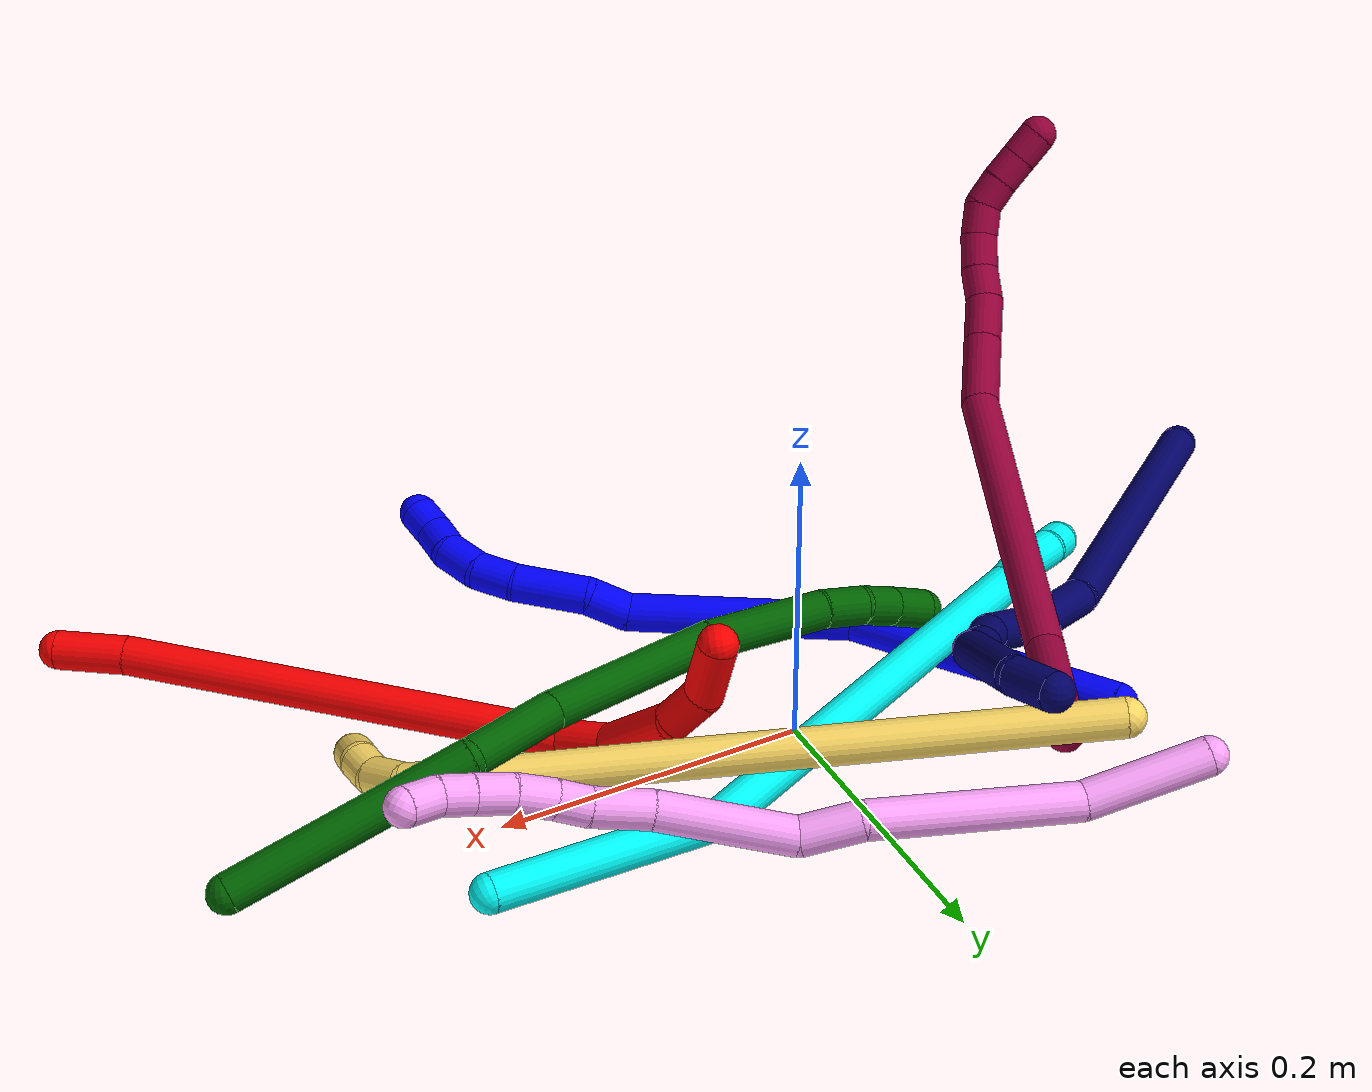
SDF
<sdf version="1.7">
 <world name="default">
  <plugin name="TubeGeneratorPlugin" filename="libtube_generator_plugin.so"/>
  <model name="photoneo_s_sensor">
   <static>1</static>
   <pose>0 0 2 1.57079 1.57079 3.14159</pose>
   <link name="link">
    <inertial><mass>0.1</mass></inertial>
    <sensor name="sensor" type="depth">
     <update_rate>30</update_rate>
     <camera>
      <horizontal_fov>1.22</horizontal_fov>
      <image><width>1920</width><height>1200</height><format>B8G8R8</format></image>
      <clip><near>0.1</near><far>4</far></clip>
      <depth_camera><output>points</output></depth_camera>
     </camera>
     <plugin name="camera_plugin" filename="libgazebo_ros_depth_camera.so">
      <baseline>0.2</baseline>
      <alwaysOn>1</alwaysOn>
      <updateRate>0.0</updateRate>
      <cameraName>camera_ir</cameraName>
      <imageTopicName>/camera/color/image_raw</imageTopicName>
      <cameraInfoTopicName>/camera/color/camera_info</cameraInfoTopicName>
      <depthImageTopicName>/camera/depth/image_raw</depthImageTopicName>
      <depthImageCameraInfoTopicName>/camera/depth/camera_info</depthImageCameraInfoTopicName>
      <pointCloudTopicName>/camera/depth/points</pointCloudTopicName>
      <frameName>fr_optical</frameName>
      <pointCloudCutoff>0.1</pointCloudCutoff>
      <pointCloudCutoffMax>2.0</pointCloudCutoffMax>
      <distortionK1>0</distortionK1>
      <distortionK2>0</distortionK2>
      <distortionK3>0</distortionK3>
      <distortionT1>0</distortionT1>
      <distortionT2>0</distortionT2>
      <CxPrime>0</CxPrime>
      <Cx>0</Cx>
      <Cy>0</Cy>
      <focalLength>0</focalLength>
      <hackBaseline>0</hackBaseline>
     </plugin>
    </sensor>
   </link>
  </model>
  <gravity>0 0 -9.8</gravity>
  <magnetic_field>6e-06 2.3e-05 -4.2e-05</magnetic_field>
  <atmosphere type="adiabatic"/>
  <physics name="default_physics" default="0" type="ode">
   <max_step_size>0.003</max_step_size>
   <real_time_factor>1</real_time_factor>
   <real_time_update_rate>1000</real_time_update_rate>
   <max_contacts>10000</max_contacts>
   <ode>
    <solver>
     <type>quick</type>
     <iters>100</iters>
     <sor>1.3</sor>
     <use_dynamic_moi_rescaling>0</use_dynamic_moi_rescaling>
    </solver>
    <constraints>
     <contact_max_correcting_vel>0</contact_max_correcting_vel>
     <contact_surface_layer>0.001</contact_surface_layer>
     <cfm>0</cfm>
     <erp>0.2</erp>
    </constraints>
   </ode>
  </physics>
  <scene><ambient>0.4 0.4 0.4 1</ambient><background>0.7 0.7 0.7 1</background><shadows>0</shadows></scene>
  <audio><device>default</device></audio>
  <spherical_coordinates>
   <surface_model>EARTH_WGS84</surface_model>
   <latitude_deg>0</latitude_deg>
   <longitude_deg>0</longitude_deg>
   <elevation>0</elevation>
   <heading_deg>0</heading_deg>
  </spherical_coordinates>
  <model name="bin">
   <static>1</static>
   <link name="bottom">
    <collision name="collision-bottom">
     <pose>0 0 -0.01 0 -0 0</pose>
     <geometry><box><size>0.8 0.6 0.02</size></box></geometry>
     <surface>
      <friction><ode><mu>100</mu><mu2>100</mu2></ode></friction>
      <contact><collide_bitmask>65535</collide_bitmask></contact>
     </surface>
    </collision>
   </link>
   <link name="west_wall">
    <collision name="collision-west_wall">
     <pose>-0.41 0 0.1 0 -0 0</pose>
     <geometry><box><size>0.02 0.6 0.2</size></box></geometry>
     <surface>
      <friction><ode><mu>100</mu><mu2>100</mu2></ode></friction>
      <contact><collide_bitmask>65535</collide_bitmask></contact>
     </surface>
    </collision>
   </link>
   <link name="east_wall">
    <collision name="collision-east_wall">
     <pose>0.41 0 0.1 0 -0 0</pose>
     <geometry><box><size>0.02 0.6 0.2</size></box></geometry>
     <surface>
      <friction><ode><mu>100</mu><mu2>100</mu2></ode></friction>
      <contact><collide_bitmask>65535</collide_bitmask></contact>
     </surface>
    </collision>
   </link>
   <link name="south_wall">
    <collision name="collision-south_wall">
     <pose>0 -0.31 0.1 0 -0 0</pose>
     <geometry><box><size>0.8 0.02 0.2</size></box></geometry>
     <surface>
      <friction><ode><mu>100</mu><mu2>100</mu2></ode></friction>
      <contact><collide_bitmask>65535</collide_bitmask></contact>
     </surface>
    </collision>
   </link>
   <link name="north_wall">
    <collision name="collision-north_wall">
     <pose>0 0.31 0.1 0 -0 0</pose>
     <geometry><box><size>0.8 0.02 0.2</size></box></geometry>
     <surface>
      <friction><ode><mu>100</mu><mu2>100</mu2></ode></friction>
      <contact><collide_bitmask>65535</collide_bitmask></contact>
     </surface>
    </collision>
   </link>
  </model>
  <model name="1">
   <static>0</static>
   <link name="1">
    <collision name="collision-cylinder-e_1_1_4">
     <pose>0.039187 -0.059771 0.056711 0.811661 0.443946 0.193348</pose>
     <geometry><cylinder><radius>0.0125</radius><length>0.182475</length></cylinder></geometry>
     <surface>
      <friction><ode><mu>1.16</mu><mu2>1.16</mu2><slip1>0</slip1><slip2>0</slip2></ode></friction>
      <contact><ode><kp>1e+06</kp><kd>1</kd><max_vel>0</max_vel><min_depth>0.001</min_depth></ode></contact>
     </surface>
    </collision>
    <visual name="visual-cylinder-e_1_1_4">
     <pose>0.039187 -0.059771 0.056711 0.811661 0.443946 0.193348</pose>
     <geometry><cylinder><radius>0.0125</radius><length>0.182475</length></cylinder></geometry>
     <material><ambient>0 0 1 1</ambient></material>
    </visual>
    <collision name="collision-cylinder-e_2_4_5">
     <pose>0.127012 -0.142189 0.162715 0.430673 0.730932 0.167006</pose>
     <geometry><cylinder><radius>0.0125</radius><length>0.145716</length></cylinder></geometry>
     <surface>
      <friction><ode><mu>1.16</mu><mu2>1.16</mu2><slip1>0</slip1><slip2>0</slip2></ode></friction>
      <contact><ode><kp>1e+06</kp><kd>1</kd><max_vel>0</max_vel><min_depth>0.001</min_depth></ode></contact>
     </surface>
    </collision>
    <visual name="visual-cylinder-e_2_4_5">
     <pose>0.127012 -0.142189 0.162715 0.430673 0.730932 0.167006</pose>
     <geometry><cylinder><radius>0.0125</radius><length>0.145716</length></cylinder></geometry>
     <material><ambient>0 0 1 1</ambient></material>
    </visual>
    <collision name="collision-cylinder-e_3_5_6">
     <pose>0.180718 -0.166792 0.22497 0.149816 0.368931 0.028004</pose>
     <geometry><cylinder><radius>0.0125</radius><length>0.028108</length></cylinder></geometry>
     <surface>
      <friction><ode><mu>1.16</mu><mu2>1.16</mu2><slip1>0</slip1><slip2>0</slip2></ode></friction>
      <contact><ode><kp>1e+06</kp><kd>1</kd><max_vel>0</max_vel><min_depth>0.001</min_depth></ode></contact>
     </surface>
    </collision>
    <visual name="visual-cylinder-e_3_5_6">
     <pose>0.180718 -0.166792 0.22497 0.149816 0.368931 0.028004</pose>
     <geometry><cylinder><radius>0.0125</radius><length>0.028108</length></cylinder></geometry>
     <material><ambient>0 0 1 1</ambient></material>
    </visual>
    <collision name="collision-cylinder-e_4_6_7">
     <pose>0.199293 -0.178709 0.255341 0.519669 0.592683 0.161987</pose>
     <geometry><cylinder><radius>0.0125</radius><length>0.048363</length></cylinder></geometry>
     <surface>
      <friction><ode><mu>1.16</mu><mu2>1.16</mu2><slip1>0</slip1><slip2>0</slip2></ode></friction>
      <contact><ode><kp>1e+06</kp><kd>1</kd><max_vel>0</max_vel><min_depth>0.001</min_depth></ode></contact>
     </surface>
    </collision>
    <visual name="visual-cylinder-e_4_6_7">
     <pose>0.199293 -0.178709 0.255341 0.519669 0.592683 0.161987</pose>
     <geometry><cylinder><radius>0.0125</radius><length>0.048363</length></cylinder></geometry>
     <material><ambient>0 0 1 1</ambient></material>
    </visual>
    <collision name="collision-cylinder-e_5_7_8">
     <pose>0.218676 -0.196447 0.282077 0.695082 0.450585 0.165661</pose>
     <geometry><cylinder><radius>0.0125</radius><length>0.026983</length></cylinder></geometry>
     <surface>
      <friction><ode><mu>1.16</mu><mu2>1.16</mu2><slip1>0</slip1><slip2>0</slip2></ode></friction>
      <contact><ode><kp>1e+06</kp><kd>1</kd><max_vel>0</max_vel><min_depth>0.001</min_depth></ode></contact>
     </surface>
    </collision>
    <visual name="visual-cylinder-e_5_7_8">
     <pose>0.218676 -0.196447 0.282077 0.695082 0.450585 0.165661</pose>
     <geometry><cylinder><radius>0.0125</radius><length>0.026983</length></cylinder></geometry>
     <material><ambient>0 0 1 1</ambient></material>
    </visual>
    <collision name="collision-cylinder-e_6_8_9">
     <pose>0.226963 -0.214165 0.299725 0.87385 0.183948 0.086099</pose>
     <geometry><cylinder><radius>0.0125</radius><length>0.026369</length></cylinder></geometry>
     <surface>
      <friction><ode><mu>1.16</mu><mu2>1.16</mu2><slip1>0</slip1><slip2>0</slip2></ode></friction>
      <contact><ode><kp>1e+06</kp><kd>1</kd><max_vel>0</max_vel><min_depth>0.001</min_depth></ode></contact>
     </surface>
    </collision>
    <visual name="visual-cylinder-e_6_8_9">
     <pose>0.226963 -0.214165 0.299725 0.87385 0.183948 0.086099</pose>
     <geometry><cylinder><radius>0.0125</radius><length>0.026369</length></cylinder></geometry>
     <material><ambient>0 0 1 1</ambient></material>
    </visual>
    <collision name="collision-cylinder-e_7_9_10">
     <pose>0.228543 -0.234068 0.312589 1.14286 -0.075789 -0.048745</pose>
     <geometry><cylinder><radius>0.0125</radius><length>0.021963</length></cylinder></geometry>
     <surface>
      <friction><ode><mu>1.16</mu><mu2>1.16</mu2><slip1>0</slip1><slip2>0</slip2></ode></friction>
      <contact><ode><kp>1e+06</kp><kd>1</kd><max_vel>0</max_vel><min_depth>0.001</min_depth></ode></contact>
     </surface>
    </collision>
    <visual name="visual-cylinder-e_7_9_10">
     <pose>0.228543 -0.234068 0.312589 1.14286 -0.075789 -0.048745</pose>
     <geometry><cylinder><radius>0.0125</radius><length>0.021963</length></cylinder></geometry>
     <material><ambient>0 0 1 1</ambient></material>
    </visual>
    <collision name="collision-cylinder-e_8_10_2">
     <pose>0.227213 -0.251985 0.323191 0.920026 -0.049838 -0.024697</pose>
     <geometry><cylinder><radius>0.0125</radius><length>0.020021</length></cylinder></geometry>
     <surface>
      <friction><ode><mu>1.16</mu><mu2>1.16</mu2><slip1>0</slip1><slip2>0</slip2></ode></friction>
      <contact><ode><kp>1e+06</kp><kd>1</kd><max_vel>0</max_vel><min_depth>0.001</min_depth></ode></contact>
     </surface>
    </collision>
    <visual name="visual-cylinder-e_8_10_2">
     <pose>0.227213 -0.251985 0.323191 0.920026 -0.049838 -0.024697</pose>
     <geometry><cylinder><radius>0.0125</radius><length>0.020021</length></cylinder></geometry>
     <material><ambient>0 0 1 1</ambient></material>
    </visual>
    <collision name="collision-sphere-2">
     <pose>0.226714 -0.25994 0.329248 0 -0 0</pose>
     <geometry><sphere><radius>0.0125</radius></sphere></geometry>
     <surface>
      <friction><ode><mu>1.16</mu><mu2>1.16</mu2><slip1>0</slip1><slip2>0</slip2></ode></friction>
      <contact><ode><kp>1e+06</kp><kd>1</kd><max_vel>0</max_vel><min_depth>0.001</min_depth></ode></contact>
     </surface>
    </collision>
    <visual name="visual-sphere-2">
     <pose>0.226714 -0.25994 0.329248 0 -0 0</pose>
     <geometry><sphere><radius>0.0125</radius></sphere></geometry>
     <material><ambient>0 0 1 1</ambient></material>
    </visual>
    <collision name="collision-sphere-10">
     <pose>0.227712 -0.24403 0.317134 0 -0 0</pose>
     <geometry><sphere><radius>0.0125</radius></sphere></geometry>
     <surface>
      <friction><ode><mu>1.16</mu><mu2>1.16</mu2><slip1>0</slip1><slip2>0</slip2></ode></friction>
      <contact><ode><kp>1e+06</kp><kd>1</kd><max_vel>0</max_vel><min_depth>0.001</min_depth></ode></contact>
     </surface>
    </collision>
    <visual name="visual-sphere-10">
     <pose>0.227712 -0.24403 0.317134 0 -0 0</pose>
     <geometry><sphere><radius>0.0125</radius></sphere></geometry>
     <material><ambient>0 0 1 1</ambient></material>
    </visual>
    <collision name="collision-sphere-9">
     <pose>0.229375 -0.224105 0.308045 0 -0 0</pose>
     <geometry><sphere><radius>0.0125</radius></sphere></geometry>
     <surface>
      <friction><ode><mu>1.16</mu><mu2>1.16</mu2><slip1>0</slip1><slip2>0</slip2></ode></friction>
      <contact><ode><kp>1e+06</kp><kd>1</kd><max_vel>0</max_vel><min_depth>0.001</min_depth></ode></contact>
     </surface>
    </collision>
    <visual name="visual-sphere-9">
     <pose>0.229375 -0.224105 0.308045 0 -0 0</pose>
     <geometry><sphere><radius>0.0125</radius></sphere></geometry>
     <material><ambient>0 0 1 1</ambient></material>
    </visual>
    <collision name="collision-sphere-4">
     <pose>0.078374 -0.119542 0.113422 0 -0 0</pose>
     <geometry><sphere><radius>0.0125</radius></sphere></geometry>
     <surface>
      <friction><ode><mu>1.16</mu><mu2>1.16</mu2><slip1>0</slip1><slip2>0</slip2></ode></friction>
      <contact><ode><kp>1e+06</kp><kd>1</kd><max_vel>0</max_vel><min_depth>0.001</min_depth></ode></contact>
     </surface>
    </collision>
    <visual name="visual-sphere-4">
     <pose>0.078374 -0.119542 0.113422 0 -0 0</pose>
     <geometry><sphere><radius>0.0125</radius></sphere></geometry>
     <material><ambient>0 0 1 1</ambient></material>
    </visual>
    <collision name="collision-sphere-1">
     <geometry><sphere><radius>0.0125</radius></sphere></geometry>
     <surface>
      <friction><ode><mu>1.16</mu><mu2>1.16</mu2><slip1>0</slip1><slip2>0</slip2></ode></friction>
      <contact><ode><kp>1e+06</kp><kd>1</kd><max_vel>0</max_vel><min_depth>0.001</min_depth></ode></contact>
     </surface>
    </collision>
    <visual name="visual-sphere-1">
     <geometry><sphere><radius>0.0125</radius></sphere></geometry>
     <material><ambient>0 0 1 1</ambient></material>
    </visual>
    <collision name="collision-sphere-8">
     <pose>0.224552 -0.204226 0.291405 0 -0 0</pose>
     <geometry><sphere><radius>0.0125</radius></sphere></geometry>
     <surface>
      <friction><ode><mu>1.16</mu><mu2>1.16</mu2><slip1>0</slip1><slip2>0</slip2></ode></friction>
      <contact><ode><kp>1e+06</kp><kd>1</kd><max_vel>0</max_vel><min_depth>0.001</min_depth></ode></contact>
     </surface>
    </collision>
    <visual name="visual-sphere-8">
     <pose>0.224552 -0.204226 0.291405 0 -0 0</pose>
     <geometry><sphere><radius>0.0125</radius></sphere></geometry>
     <material><ambient>0 0 1 1</ambient></material>
    </visual>
    <collision name="collision-sphere-5">
     <pose>0.175649 -0.164836 0.212008 0 -0 0</pose>
     <geometry><sphere><radius>0.0125</radius></sphere></geometry>
     <surface>
      <friction><ode><mu>1.16</mu><mu2>1.16</mu2><slip1>0</slip1><slip2>0</slip2></ode></friction>
      <contact><ode><kp>1e+06</kp><kd>1</kd><max_vel>0</max_vel><min_depth>0.001</min_depth></ode></contact>
     </surface>
    </collision>
    <visual name="visual-sphere-5">
     <pose>0.175649 -0.164836 0.212008 0 -0 0</pose>
     <geometry><sphere><radius>0.0125</radius></sphere></geometry>
     <material><ambient>0 0 1 1</ambient></material>
    </visual>
    <collision name="collision-sphere-6">
     <pose>0.185786 -0.168749 0.237931 0 -0 0</pose>
     <geometry><sphere><radius>0.0125</radius></sphere></geometry>
     <surface>
      <friction><ode><mu>1.16</mu><mu2>1.16</mu2><slip1>0</slip1><slip2>0</slip2></ode></friction>
      <contact><ode><kp>1e+06</kp><kd>1</kd><max_vel>0</max_vel><min_depth>0.001</min_depth></ode></contact>
     </surface>
    </collision>
    <visual name="visual-sphere-6">
     <pose>0.185786 -0.168749 0.237931 0 -0 0</pose>
     <geometry><sphere><radius>0.0125</radius></sphere></geometry>
     <material><ambient>0 0 1 1</ambient></material>
    </visual>
    <collision name="collision-sphere-7">
     <pose>0.212801 -0.188669 0.27275 0 -0 0</pose>
     <geometry><sphere><radius>0.0125</radius></sphere></geometry>
     <surface>
      <friction><ode><mu>1.16</mu><mu2>1.16</mu2><slip1>0</slip1><slip2>0</slip2></ode></friction>
      <contact><ode><kp>1e+06</kp><kd>1</kd><max_vel>0</max_vel><min_depth>0.001</min_depth></ode></contact>
     </surface>
    </collision>
    <visual name="visual-sphere-7">
     <pose>0.212801 -0.188669 0.27275 0 -0 0</pose>
     <geometry><sphere><radius>0.0125</radius></sphere></geometry>
     <material><ambient>0 0 1 1</ambient></material>
    </visual>
    <inertial>
     <pose>0.123661 -0.132182 0.163164 0 -0 0</pose>
     <mass>0.5</mass>
     <inertia><ixx>0.00081</ixx><ixy>0</ixy><ixz>0</ixz><iyy>0.000748</iyy><iyz>0</iyz><izz>5e-05</izz></inertia>
    </inertial>
   </link>
   <pose>-0.185628 0.080844 0.011471 0.40458 0.630309 0.046603</pose>
  </model>
  <model name="2">
   <static>0</static>
   <link name="2">
    <collision name="collision-cylinder-e_1_1_4">
     <pose>0.000719 0.005995 -0.02243 -2.88041 0.030954 -0.234617</pose>
     <geometry><cylinder><radius>0.0125</radius><length>0.046457</length></cylinder></geometry>
     <surface>
      <friction><ode><mu>1.16</mu><mu2>1.16</mu2><slip1>0</slip1><slip2>0</slip2></ode></friction>
      <contact><ode><kp>1e+06</kp><kd>1</kd><max_vel>0</max_vel><min_depth>0.001</min_depth></ode></contact>
     </surface>
    </collision>
    <visual name="visual-cylinder-e_1_1_4">
     <pose>0.000719 0.005995 -0.02243 -2.88041 0.030954 -0.234617</pose>
     <geometry><cylinder><radius>0.0125</radius><length>0.046457</length></cylinder></geometry>
     <material><ambient>1 0 0 1</ambient></material>
    </visual>
    <collision name="collision-cylinder-e_2_4_5">
     <pose>0.00504 0.060829 -0.16803 -2.7641 0.027179 -0.142051</pose>
     <geometry><cylinder><radius>0.0125</radius><length>0.265097</length></cylinder></geometry>
     <surface>
      <friction><ode><mu>1.16</mu><mu2>1.16</mu2><slip1>0</slip1><slip2>0</slip2></ode></friction>
      <contact><ode><kp>1e+06</kp><kd>1</kd><max_vel>0</max_vel><min_depth>0.001</min_depth></ode></contact>
     </surface>
    </collision>
    <visual name="visual-cylinder-e_2_4_5">
     <pose>0.00504 0.060829 -0.16803 -2.7641 0.027179 -0.142051</pose>
     <geometry><cylinder><radius>0.0125</radius><length>0.265097</length></cylinder></geometry>
     <material><ambient>1 0 0 1</ambient></material>
    </visual>
    <collision name="collision-cylinder-e_3_5_6">
     <pose>0.008784 0.114562 -0.303078 -2.7507 0.011045 -0.055777</pose>
     <geometry><cylinder><radius>0.0125</radius><length>0.025696</length></cylinder></geometry>
     <surface>
      <friction><ode><mu>1.16</mu><mu2>1.16</mu2><slip1>0</slip1><slip2>0</slip2></ode></friction>
      <contact><ode><kp>1e+06</kp><kd>1</kd><max_vel>0</max_vel><min_depth>0.001</min_depth></ode></contact>
     </surface>
    </collision>
    <visual name="visual-cylinder-e_3_5_6">
     <pose>0.008784 0.114562 -0.303078 -2.7507 0.011045 -0.055777</pose>
     <geometry><cylinder><radius>0.0125</radius><length>0.025696</length></cylinder></geometry>
     <material><ambient>1 0 0 1</ambient></material>
    </visual>
    <collision name="collision-cylinder-e_4_6_7">
     <pose>0.003101 0.127004 -0.330065 -2.67837 -0.332118 1.23568</pose>
     <geometry><cylinder><radius>0.0125</radius><length>0.035731</length></cylinder></geometry>
     <surface>
      <friction><ode><mu>1.16</mu><mu2>1.16</mu2><slip1>0</slip1><slip2>0</slip2></ode></friction>
      <contact><ode><kp>1e+06</kp><kd>1</kd><max_vel>0</max_vel><min_depth>0.001</min_depth></ode></contact>
     </surface>
    </collision>
    <visual name="visual-cylinder-e_4_6_7">
     <pose>0.003101 0.127004 -0.330065 -2.67837 -0.332118 1.23568</pose>
     <geometry><cylinder><radius>0.0125</radius><length>0.035731</length></cylinder></geometry>
     <material><ambient>1 0 0 1</ambient></material>
    </visual>
    <collision name="collision-cylinder-e_5_7_8">
     <pose>-0.021669 0.140939 -0.365962 -2.8434 -0.716639 2.37866</pose>
     <geometry><cylinder><radius>0.0125</radius><length>0.057684</length></cylinder></geometry>
     <surface>
      <friction><ode><mu>1.16</mu><mu2>1.16</mu2><slip1>0</slip1><slip2>0</slip2></ode></friction>
      <contact><ode><kp>1e+06</kp><kd>1</kd><max_vel>0</max_vel><min_depth>0.001</min_depth></ode></contact>
     </surface>
    </collision>
    <visual name="visual-cylinder-e_5_7_8">
     <pose>-0.021669 0.140939 -0.365962 -2.8434 -0.716639 2.37866</pose>
     <geometry><cylinder><radius>0.0125</radius><length>0.057684</length></cylinder></geometry>
     <material><ambient>1 0 0 1</ambient></material>
    </visual>
    <collision name="collision-cylinder-e_6_8_9">
     <pose>-0.049547 0.145069 -0.398004 2.94347 -0.661326 -2.57794</pose>
     <geometry><cylinder><radius>0.0125</radius><length>0.029089</length></cylinder></geometry>
     <surface>
      <friction><ode><mu>1.16</mu><mu2>1.16</mu2><slip1>0</slip1><slip2>0</slip2></ode></friction>
      <contact><ode><kp>1e+06</kp><kd>1</kd><max_vel>0</max_vel><min_depth>0.001</min_depth></ode></contact>
     </surface>
    </collision>
    <visual name="visual-cylinder-e_6_8_9">
     <pose>-0.049547 0.145069 -0.398004 2.94347 -0.661326 -2.57794</pose>
     <geometry><cylinder><radius>0.0125</radius><length>0.029089</length></cylinder></geometry>
     <material><ambient>1 0 0 1</ambient></material>
    </visual>
    <collision name="collision-cylinder-e_7_9_2">
     <pose>-0.076272 0.137171 -0.41678 2.49837 -1.08468 -2.13148</pose>
     <geometry><cylinder><radius>0.0125</radius><length>0.040247</length></cylinder></geometry>
     <surface>
      <friction><ode><mu>1.16</mu><mu2>1.16</mu2><slip1>0</slip1><slip2>0</slip2></ode></friction>
      <contact><ode><kp>1e+06</kp><kd>1</kd><max_vel>0</max_vel><min_depth>0.001</min_depth></ode></contact>
     </surface>
    </collision>
    <visual name="visual-cylinder-e_7_9_2">
     <pose>-0.076272 0.137171 -0.41678 2.49837 -1.08468 -2.13148</pose>
     <geometry><cylinder><radius>0.0125</radius><length>0.040247</length></cylinder></geometry>
     <material><ambient>1 0 0 1</ambient></material>
    </visual>
    <collision name="collision-sphere-2">
     <pose>-0.094064 0.131532 -0.424303 0 -0 0</pose>
     <geometry><sphere><radius>0.0125</radius></sphere></geometry>
     <surface>
      <friction><ode><mu>1.16</mu><mu2>1.16</mu2><slip1>0</slip1><slip2>0</slip2></ode></friction>
      <contact><ode><kp>1e+06</kp><kd>1</kd><max_vel>0</max_vel><min_depth>0.001</min_depth></ode></contact>
     </surface>
    </collision>
    <visual name="visual-sphere-2">
     <pose>-0.094064 0.131532 -0.424303 0 -0 0</pose>
     <geometry><sphere><radius>0.0125</radius></sphere></geometry>
     <material><ambient>1 0 0 1</ambient></material>
    </visual>
    <collision name="collision-sphere-9">
     <pose>-0.05848 0.14281 -0.409257 0 -0 0</pose>
     <geometry><sphere><radius>0.0125</radius></sphere></geometry>
     <surface>
      <friction><ode><mu>1.16</mu><mu2>1.16</mu2><slip1>0</slip1><slip2>0</slip2></ode></friction>
      <contact><ode><kp>1e+06</kp><kd>1</kd><max_vel>0</max_vel><min_depth>0.001</min_depth></ode></contact>
     </surface>
    </collision>
    <visual name="visual-sphere-9">
     <pose>-0.05848 0.14281 -0.409257 0 -0 0</pose>
     <geometry><sphere><radius>0.0125</radius></sphere></geometry>
     <material><ambient>1 0 0 1</ambient></material>
    </visual>
    <collision name="collision-sphere-4">
     <pose>0.001438 0.011991 -0.04486 0 -0 0</pose>
     <geometry><sphere><radius>0.0125</radius></sphere></geometry>
     <surface>
      <friction><ode><mu>1.16</mu><mu2>1.16</mu2><slip1>0</slip1><slip2>0</slip2></ode></friction>
      <contact><ode><kp>1e+06</kp><kd>1</kd><max_vel>0</max_vel><min_depth>0.001</min_depth></ode></contact>
     </surface>
    </collision>
    <visual name="visual-sphere-4">
     <pose>0.001438 0.011991 -0.04486 0 -0 0</pose>
     <geometry><sphere><radius>0.0125</radius></sphere></geometry>
     <material><ambient>1 0 0 1</ambient></material>
    </visual>
    <collision name="collision-sphere-1">
     <geometry><sphere><radius>0.0125</radius></sphere></geometry>
     <surface>
      <friction><ode><mu>1.16</mu><mu2>1.16</mu2><slip1>0</slip1><slip2>0</slip2></ode></friction>
      <contact><ode><kp>1e+06</kp><kd>1</kd><max_vel>0</max_vel><min_depth>0.001</min_depth></ode></contact>
     </surface>
    </collision>
    <visual name="visual-sphere-1">
     <geometry><sphere><radius>0.0125</radius></sphere></geometry>
     <material><ambient>1 0 0 1</ambient></material>
    </visual>
    <collision name="collision-sphere-8">
     <pose>-0.040614 0.147329 -0.38675 0 -0 0</pose>
     <geometry><sphere><radius>0.0125</radius></sphere></geometry>
     <surface>
      <friction><ode><mu>1.16</mu><mu2>1.16</mu2><slip1>0</slip1><slip2>0</slip2></ode></friction>
      <contact><ode><kp>1e+06</kp><kd>1</kd><max_vel>0</max_vel><min_depth>0.001</min_depth></ode></contact>
     </surface>
    </collision>
    <visual name="visual-sphere-8">
     <pose>-0.040614 0.147329 -0.38675 0 -0 0</pose>
     <geometry><sphere><radius>0.0125</radius></sphere></geometry>
     <material><ambient>1 0 0 1</ambient></material>
    </visual>
    <collision name="collision-sphere-5">
     <pose>0.008642 0.109667 -0.2912 0 -0 0</pose>
     <geometry><sphere><radius>0.0125</radius></sphere></geometry>
     <surface>
      <friction><ode><mu>1.16</mu><mu2>1.16</mu2><slip1>0</slip1><slip2>0</slip2></ode></friction>
      <contact><ode><kp>1e+06</kp><kd>1</kd><max_vel>0</max_vel><min_depth>0.001</min_depth></ode></contact>
     </surface>
    </collision>
    <visual name="visual-sphere-5">
     <pose>0.008642 0.109667 -0.2912 0 -0 0</pose>
     <geometry><sphere><radius>0.0125</radius></sphere></geometry>
     <material><ambient>1 0 0 1</ambient></material>
    </visual>
    <collision name="collision-sphere-6">
     <pose>0.008926 0.119457 -0.314956 0 -0 0</pose>
     <geometry><sphere><radius>0.0125</radius></sphere></geometry>
     <surface>
      <friction><ode><mu>1.16</mu><mu2>1.16</mu2><slip1>0</slip1><slip2>0</slip2></ode></friction>
      <contact><ode><kp>1e+06</kp><kd>1</kd><max_vel>0</max_vel><min_depth>0.001</min_depth></ode></contact>
     </surface>
    </collision>
    <visual name="visual-sphere-6">
     <pose>0.008926 0.119457 -0.314956 0 -0 0</pose>
     <geometry><sphere><radius>0.0125</radius></sphere></geometry>
     <material><ambient>1 0 0 1</ambient></material>
    </visual>
    <collision name="collision-sphere-7">
     <pose>-0.002724 0.13455 -0.345175 0 -0 0</pose>
     <geometry><sphere><radius>0.0125</radius></sphere></geometry>
     <surface>
      <friction><ode><mu>1.16</mu><mu2>1.16</mu2><slip1>0</slip1><slip2>0</slip2></ode></friction>
      <contact><ode><kp>1e+06</kp><kd>1</kd><max_vel>0</max_vel><min_depth>0.001</min_depth></ode></contact>
     </surface>
    </collision>
    <visual name="visual-sphere-7">
     <pose>-0.002724 0.13455 -0.345175 0 -0 0</pose>
     <geometry><sphere><radius>0.0125</radius></sphere></geometry>
     <material><ambient>1 0 0 1</ambient></material>
    </visual>
    <inertial>
     <pose>-0.00811 0.083513 -0.229259 0 -0 0</pose>
     <mass>0.5</mass>
     <inertia>
      <ixx>0.001326</ixx>
      <ixy>0</ixy>
      <ixz>0</ixz>
      <iyy>-0.001628</iyy>
      <iyz>0</iyz>
      <izz>-0.000637</izz>
     </inertia>
    </inertial>
   </link>
   <pose>0.382518 -0.275626 0.012317 -1.99977 1.12971 -2.40173</pose>
  </model>
  <model name="3">
   <static>0</static>
   <link name="3">
    <collision name="collision-cylinder-e_1_1_4">
     <pose>-0.069904 0.02469 -0.003287 -1.70315 -1.22851 1.35604</pose>
     <geometry><cylinder><radius>0.0125</radius><length>0.148418</length></cylinder></geometry>
     <surface>
      <friction><ode><mu>1.16</mu><mu2>1.16</mu2><slip1>0</slip1><slip2>0</slip2></ode></friction>
      <contact><ode><kp>1e+06</kp><kd>1</kd><max_vel>0</max_vel><min_depth>0.001</min_depth></ode></contact>
     </surface>
    </collision>
    <visual name="visual-cylinder-e_1_1_4">
     <pose>-0.069904 0.02469 -0.003287 -1.70315 -1.22851 1.35604</pose>
     <geometry><cylinder><radius>0.0125</radius><length>0.148418</length></cylinder></geometry>
     <material><ambient>0.003922 1 0.996078 1</ambient></material>
    </visual>
    <collision name="collision-cylinder-e_2_4_5">
     <pose>-0.257574 0.091705 -0.062852 -2.49677 -1.03188 2.07702</pose>
     <geometry><cylinder><radius>0.0125</radius><length>0.274426</length></cylinder></geometry>
     <surface>
      <friction><ode><mu>1.16</mu><mu2>1.16</mu2><slip1>0</slip1><slip2>0</slip2></ode></friction>
      <contact><ode><kp>1e+06</kp><kd>1</kd><max_vel>0</max_vel><min_depth>0.001</min_depth></ode></contact>
     </surface>
    </collision>
    <visual name="visual-cylinder-e_2_4_5">
     <pose>-0.257574 0.091705 -0.062852 -2.49677 -1.03188 2.07702</pose>
     <geometry><cylinder><radius>0.0125</radius><length>0.274426</length></cylinder></geometry>
     <material><ambient>0.003922 1 0.996078 1</ambient></material>
    </visual>
    <collision name="collision-cylinder-e_3_5_6">
     <pose>-0.384467 0.140398 -0.12665 -2.43889 -0.747206 1.63787</pose>
     <geometry><cylinder><radius>0.0125</radius><length>0.026863</length></cylinder></geometry>
     <surface>
      <friction><ode><mu>1.16</mu><mu2>1.16</mu2><slip1>0</slip1><slip2>0</slip2></ode></friction>
      <contact><ode><kp>1e+06</kp><kd>1</kd><max_vel>0</max_vel><min_depth>0.001</min_depth></ode></contact>
     </surface>
    </collision>
    <visual name="visual-cylinder-e_3_5_6">
     <pose>-0.384467 0.140398 -0.12665 -2.43889 -0.747206 1.63787</pose>
     <geometry><cylinder><radius>0.0125</radius><length>0.026863</length></cylinder></geometry>
     <material><ambient>0.003922 1 0.996078 1</ambient></material>
    </visual>
    <collision name="collision-cylinder-e_4_6_7">
     <pose>-0.404713 0.154791 -0.140382 -2.22959 -0.830937 1.46499</pose>
     <geometry><cylinder><radius>0.0125</radius><length>0.030108</length></cylinder></geometry>
     <surface>
      <friction><ode><mu>1.16</mu><mu2>1.16</mu2><slip1>0</slip1><slip2>0</slip2></ode></friction>
      <contact><ode><kp>1e+06</kp><kd>1</kd><max_vel>0</max_vel><min_depth>0.001</min_depth></ode></contact>
     </surface>
    </collision>
    <visual name="visual-cylinder-e_4_6_7">
     <pose>-0.404713 0.154791 -0.140382 -2.22959 -0.830937 1.46499</pose>
     <geometry><cylinder><radius>0.0125</radius><length>0.030108</length></cylinder></geometry>
     <material><ambient>0.003922 1 0.996078 1</ambient></material>
    </visual>
    <collision name="collision-cylinder-e_5_7_2">
     <pose>-0.421576 0.169456 -0.151571 -2.21401 -0.605561 1.11655</pose>
     <geometry><cylinder><radius>0.0125</radius><length>0.020186</length></cylinder></geometry>
     <surface>
      <friction><ode><mu>1.16</mu><mu2>1.16</mu2><slip1>0</slip1><slip2>0</slip2></ode></friction>
      <contact><ode><kp>1e+06</kp><kd>1</kd><max_vel>0</max_vel><min_depth>0.001</min_depth></ode></contact>
     </surface>
    </collision>
    <visual name="visual-cylinder-e_5_7_2">
     <pose>-0.421576 0.169456 -0.151571 -2.21401 -0.605561 1.11655</pose>
     <geometry><cylinder><radius>0.0125</radius><length>0.020186</length></cylinder></geometry>
     <material><ambient>0.003922 1 0.996078 1</ambient></material>
    </visual>
    <collision name="collision-sphere-2">
     <pose>-0.427321 0.176096 -0.156548 0 -0 0</pose>
     <geometry><sphere><radius>0.0125</radius></sphere></geometry>
     <surface>
      <friction><ode><mu>1.16</mu><mu2>1.16</mu2><slip1>0</slip1><slip2>0</slip2></ode></friction>
      <contact><ode><kp>1e+06</kp><kd>1</kd><max_vel>0</max_vel><min_depth>0.001</min_depth></ode></contact>
     </surface>
    </collision>
    <visual name="visual-sphere-2">
     <pose>-0.427321 0.176096 -0.156548 0 -0 0</pose>
     <geometry><sphere><radius>0.0125</radius></sphere></geometry>
     <material><ambient>0.003922 1 0.996078 1</ambient></material>
    </visual>
    <collision name="collision-sphere-7">
     <pose>-0.415831 0.162816 -0.146594 0 -0 0</pose>
     <geometry><sphere><radius>0.0125</radius></sphere></geometry>
     <surface>
      <friction><ode><mu>1.16</mu><mu2>1.16</mu2><slip1>0</slip1><slip2>0</slip2></ode></friction>
      <contact><ode><kp>1e+06</kp><kd>1</kd><max_vel>0</max_vel><min_depth>0.001</min_depth></ode></contact>
     </surface>
    </collision>
    <visual name="visual-sphere-7">
     <pose>-0.415831 0.162816 -0.146594 0 -0 0</pose>
     <geometry><sphere><radius>0.0125</radius></sphere></geometry>
     <material><ambient>0.003922 1 0.996078 1</ambient></material>
    </visual>
    <collision name="collision-sphere-6">
     <pose>-0.393595 0.146766 -0.134169 0 -0 0</pose>
     <geometry><sphere><radius>0.0125</radius></sphere></geometry>
     <surface>
      <friction><ode><mu>1.16</mu><mu2>1.16</mu2><slip1>0</slip1><slip2>0</slip2></ode></friction>
      <contact><ode><kp>1e+06</kp><kd>1</kd><max_vel>0</max_vel><min_depth>0.001</min_depth></ode></contact>
     </surface>
    </collision>
    <visual name="visual-sphere-6">
     <pose>-0.393595 0.146766 -0.134169 0 -0 0</pose>
     <geometry><sphere><radius>0.0125</radius></sphere></geometry>
     <material><ambient>0.003922 1 0.996078 1</ambient></material>
    </visual>
    <collision name="collision-sphere-5">
     <pose>-0.375339 0.13403 -0.119131 0 -0 0</pose>
     <geometry><sphere><radius>0.0125</radius></sphere></geometry>
     <surface>
      <friction><ode><mu>1.16</mu><mu2>1.16</mu2><slip1>0</slip1><slip2>0</slip2></ode></friction>
      <contact><ode><kp>1e+06</kp><kd>1</kd><max_vel>0</max_vel><min_depth>0.001</min_depth></ode></contact>
     </surface>
    </collision>
    <visual name="visual-sphere-5">
     <pose>-0.375339 0.13403 -0.119131 0 -0 0</pose>
     <geometry><sphere><radius>0.0125</radius></sphere></geometry>
     <material><ambient>0.003922 1 0.996078 1</ambient></material>
    </visual>
    <collision name="collision-sphere-1">
     <geometry><sphere><radius>0.0125</radius></sphere></geometry>
     <surface>
      <friction><ode><mu>1.16</mu><mu2>1.16</mu2><slip1>0</slip1><slip2>0</slip2></ode></friction>
      <contact><ode><kp>1e+06</kp><kd>1</kd><max_vel>0</max_vel><min_depth>0.001</min_depth></ode></contact>
     </surface>
    </collision>
    <visual name="visual-sphere-1">
     <geometry><sphere><radius>0.0125</radius></sphere></geometry>
     <material><ambient>0.003922 1 0.996078 1</ambient></material>
    </visual>
    <collision name="collision-sphere-4">
     <pose>-0.139809 0.049379 -0.006574 0 -0 0</pose>
     <geometry><sphere><radius>0.0125</radius></sphere></geometry>
     <surface>
      <friction><ode><mu>1.16</mu><mu2>1.16</mu2><slip1>0</slip1><slip2>0</slip2></ode></friction>
      <contact><ode><kp>1e+06</kp><kd>1</kd><max_vel>0</max_vel><min_depth>0.001</min_depth></ode></contact>
     </surface>
    </collision>
    <visual name="visual-sphere-4">
     <pose>-0.139809 0.049379 -0.006574 0 -0 0</pose>
     <geometry><sphere><radius>0.0125</radius></sphere></geometry>
     <material><ambient>0.003922 1 0.996078 1</ambient></material>
    </visual>
    <inertial>
     <pose>-0.224165 0.081366 -0.056849 0 -0 0</pose>
     <mass>0.5</mass>
     <inertia>
      <ixx>0.00043</ixx>
      <ixy>0</ixy>
      <ixz>0</ixz>
      <iyy>0.002591</iyy>
      <iyz>0</iyz>
      <izz>0.001111</izz>
     </inertia>
    </inertial>
   </link>
   <pose>0.23691 0.063755 0.012567 -1.88089 0.310972 -0.163628</pose>
  </model>
  <model name="4">
   <static>0</static>
   <link name="4">
    <collision name="collision-cylinder-e_1_1_4">
     <pose>0.025661 -0.013452 -0.028637 2.70243 0.681448 2.01799</pose>
     <geometry><cylinder><radius>0.0125</radius><length>0.081475</length></cylinder></geometry>
     <surface>
      <friction><ode><mu>1.16</mu><mu2>1.16</mu2><slip1>0</slip1><slip2>0</slip2></ode></friction>
      <contact><ode><kp>1e+06</kp><kd>1</kd><max_vel>0</max_vel><min_depth>0.001</min_depth></ode></contact>
     </surface>
    </collision>
    <visual name="visual-cylinder-e_1_1_4">
     <pose>0.025661 -0.013452 -0.028637 2.70243 0.681448 2.01799</pose>
     <geometry><cylinder><radius>0.0125</radius><length>0.081475</length></cylinder></geometry>
     <material><ambient>1 0.65098 0.996078 1</ambient></material>
    </visual>
    <collision name="collision-cylinder-e_2_4_5">
     <pose>0.109843 -0.044661 -0.089784 2.64168 1.00647 2.27315</pose>
     <geometry><cylinder><radius>0.0125</radius><length>0.138519</length></cylinder></geometry>
     <surface>
      <friction><ode><mu>1.16</mu><mu2>1.16</mu2><slip1>0</slip1><slip2>0</slip2></ode></friction>
      <contact><ode><kp>1e+06</kp><kd>1</kd><max_vel>0</max_vel><min_depth>0.001</min_depth></ode></contact>
     </surface>
    </collision>
    <visual name="visual-cylinder-e_2_4_5">
     <pose>0.109843 -0.044661 -0.089784 2.64168 1.00647 2.27315</pose>
     <geometry><cylinder><radius>0.0125</radius><length>0.138519</length></cylinder></geometry>
     <material><ambient>1 0.65098 0.996078 1</ambient></material>
    </visual>
    <collision name="collision-cylinder-e_3_5_6">
     <pose>0.180262 -0.071548 -0.13488 2.51402 0.653156 1.61361</pose>
     <geometry><cylinder><radius>0.0125</radius><length>0.039158</length></cylinder></geometry>
     <surface>
      <friction><ode><mu>1.16</mu><mu2>1.16</mu2><slip1>0</slip1><slip2>0</slip2></ode></friction>
      <contact><ode><kp>1e+06</kp><kd>1</kd><max_vel>0</max_vel><min_depth>0.001</min_depth></ode></contact>
     </surface>
    </collision>
    <visual name="visual-cylinder-e_3_5_6">
     <pose>0.180262 -0.071548 -0.13488 2.51402 0.653156 1.61361</pose>
     <geometry><cylinder><radius>0.0125</radius><length>0.039158</length></cylinder></geometry>
     <material><ambient>1 0.65098 0.996078 1</ambient></material>
    </visual>
    <collision name="collision-cylinder-e_4_6_7">
     <pose>0.22999 -0.09983 -0.158529 2.09461 1.04173 1.56473</pose>
     <geometry><cylinder><radius>0.0125</radius><length>0.087642</length></cylinder></geometry>
     <surface>
      <friction><ode><mu>1.16</mu><mu2>1.16</mu2><slip1>0</slip1><slip2>0</slip2></ode></friction>
      <contact><ode><kp>1e+06</kp><kd>1</kd><max_vel>0</max_vel><min_depth>0.001</min_depth></ode></contact>
     </surface>
    </collision>
    <visual name="visual-cylinder-e_4_6_7">
     <pose>0.22999 -0.09983 -0.158529 2.09461 1.04173 1.56473</pose>
     <geometry><cylinder><radius>0.0125</radius><length>0.087642</length></cylinder></geometry>
     <material><ambient>1 0.65098 0.996078 1</ambient></material>
    </visual>
    <collision name="collision-cylinder-e_5_7_8">
     <pose>0.284573 -0.124873 -0.176367 2.42587 1.07881 2.02482</pose>
     <geometry><cylinder><radius>0.0125</radius><length>0.038015</length></cylinder></geometry>
     <surface>
      <friction><ode><mu>1.16</mu><mu2>1.16</mu2><slip1>0</slip1><slip2>0</slip2></ode></friction>
      <contact><ode><kp>1e+06</kp><kd>1</kd><max_vel>0</max_vel><min_depth>0.001</min_depth></ode></contact>
     </surface>
    </collision>
    <visual name="visual-cylinder-e_5_7_8">
     <pose>0.284573 -0.124873 -0.176367 2.42587 1.07881 2.02482</pose>
     <geometry><cylinder><radius>0.0125</radius><length>0.038015</length></cylinder></geometry>
     <material><ambient>1 0.65098 0.996078 1</ambient></material>
    </visual>
    <collision name="collision-cylinder-e_6_8_9">
     <pose>0.311572 -0.133864 -0.185274 2.1733 1.219 1.85045</pose>
     <geometry><cylinder><radius>0.0125</radius><length>0.021831</length></cylinder></geometry>
     <surface>
      <friction><ode><mu>1.16</mu><mu2>1.16</mu2><slip1>0</slip1><slip2>0</slip2></ode></friction>
      <contact><ode><kp>1e+06</kp><kd>1</kd><max_vel>0</max_vel><min_depth>0.001</min_depth></ode></contact>
     </surface>
    </collision>
    <visual name="visual-cylinder-e_6_8_9">
     <pose>0.311572 -0.133864 -0.185274 2.1733 1.219 1.85045</pose>
     <geometry><cylinder><radius>0.0125</radius><length>0.021831</length></cylinder></geometry>
     <material><ambient>1 0.65098 0.996078 1</ambient></material>
    </visual>
    <collision name="collision-cylinder-e_7_9_10">
     <pose>0.333885 -0.139541 -0.190651 2.47024 1.23992 2.23241</pose>
     <geometry><cylinder><radius>0.0125</radius><length>0.025516</length></cylinder></geometry>
     <surface>
      <friction><ode><mu>1.16</mu><mu2>1.16</mu2><slip1>0</slip1><slip2>0</slip2></ode></friction>
      <contact><ode><kp>1e+06</kp><kd>1</kd><max_vel>0</max_vel><min_depth>0.001</min_depth></ode></contact>
     </surface>
    </collision>
    <visual name="visual-cylinder-e_7_9_10">
     <pose>0.333885 -0.139541 -0.190651 2.47024 1.23992 2.23241</pose>
     <geometry><cylinder><radius>0.0125</radius><length>0.025516</length></cylinder></geometry>
     <material><ambient>1 0.65098 0.996078 1</ambient></material>
    </visual>
    <collision name="collision-cylinder-e_8_10_11">
     <pose>0.356997 -0.14418 -0.198655 2.73288 1.13187 2.51087</pose>
     <geometry><cylinder><radius>0.0125</radius><length>0.024405</length></cylinder></geometry>
     <surface>
      <friction><ode><mu>1.16</mu><mu2>1.16</mu2><slip1>0</slip1><slip2>0</slip2></ode></friction>
      <contact><ode><kp>1e+06</kp><kd>1</kd><max_vel>0</max_vel><min_depth>0.001</min_depth></ode></contact>
     </surface>
    </collision>
    <visual name="visual-cylinder-e_8_10_11">
     <pose>0.356997 -0.14418 -0.198655 2.73288 1.13187 2.51087</pose>
     <geometry><cylinder><radius>0.0125</radius><length>0.024405</length></cylinder></geometry>
     <material><ambient>1 0.65098 0.996078 1</ambient></material>
    </visual>
    <collision name="collision-cylinder-e_9_11_12">
     <pose>0.377365 -0.147985 -0.207715 2.75641 1.10885 2.5314</pose>
     <geometry><cylinder><radius>0.0125</radius><length>0.020827</length></cylinder></geometry>
     <surface>
      <friction><ode><mu>1.16</mu><mu2>1.16</mu2><slip1>0</slip1><slip2>0</slip2></ode></friction>
      <contact><ode><kp>1e+06</kp><kd>1</kd><max_vel>0</max_vel><min_depth>0.001</min_depth></ode></contact>
     </surface>
    </collision>
    <visual name="visual-cylinder-e_9_11_12">
     <pose>0.377365 -0.147985 -0.207715 2.75641 1.10885 2.5314</pose>
     <geometry><cylinder><radius>0.0125</radius><length>0.020827</length></cylinder></geometry>
     <material><ambient>1 0.65098 0.996078 1</ambient></material>
    </visual>
    <collision name="collision-cylinder-e_10_12_2">
     <pose>0.396078 -0.148412 -0.218173 -2.93089 0.980207 -2.75027</pose>
     <geometry><cylinder><radius>0.0125</radius><length>0.022613</length></cylinder></geometry>
     <surface>
      <friction><ode><mu>1.16</mu><mu2>1.16</mu2><slip1>0</slip1><slip2>0</slip2></ode></friction>
      <contact><ode><kp>1e+06</kp><kd>1</kd><max_vel>0</max_vel><min_depth>0.001</min_depth></ode></contact>
     </surface>
    </collision>
    <visual name="visual-cylinder-e_10_12_2">
     <pose>0.396078 -0.148412 -0.218173 -2.93089 0.980207 -2.75027</pose>
     <geometry><cylinder><radius>0.0125</radius><length>0.022613</length></cylinder></geometry>
     <material><ambient>1 0.65098 0.996078 1</ambient></material>
    </visual>
    <collision name="collision-sphere-2">
     <pose>0.40547 -0.147095 -0.22433 0 -0 0</pose>
     <geometry><sphere><radius>0.0125</radius></sphere></geometry>
     <surface>
      <friction><ode><mu>1.16</mu><mu2>1.16</mu2><slip1>0</slip1><slip2>0</slip2></ode></friction>
      <contact><ode><kp>1e+06</kp><kd>1</kd><max_vel>0</max_vel><min_depth>0.001</min_depth></ode></contact>
     </surface>
    </collision>
    <visual name="visual-sphere-2">
     <pose>0.40547 -0.147095 -0.22433 0 -0 0</pose>
     <geometry><sphere><radius>0.0125</radius></sphere></geometry>
     <material><ambient>1 0.65098 0.996078 1</ambient></material>
    </visual>
    <collision name="collision-sphere-12">
     <pose>0.386687 -0.149728 -0.212016 0 -0 0</pose>
     <geometry><sphere><radius>0.0125</radius></sphere></geometry>
     <surface>
      <friction><ode><mu>1.16</mu><mu2>1.16</mu2><slip1>0</slip1><slip2>0</slip2></ode></friction>
      <contact><ode><kp>1e+06</kp><kd>1</kd><max_vel>0</max_vel><min_depth>0.001</min_depth></ode></contact>
     </surface>
    </collision>
    <visual name="visual-sphere-12">
     <pose>0.386687 -0.149728 -0.212016 0 -0 0</pose>
     <geometry><sphere><radius>0.0125</radius></sphere></geometry>
     <material><ambient>1 0.65098 0.996078 1</ambient></material>
    </visual>
    <collision name="collision-sphere-11">
     <pose>0.368043 -0.146241 -0.203414 0 -0 0</pose>
     <geometry><sphere><radius>0.0125</radius></sphere></geometry>
     <surface>
      <friction><ode><mu>1.16</mu><mu2>1.16</mu2><slip1>0</slip1><slip2>0</slip2></ode></friction>
      <contact><ode><kp>1e+06</kp><kd>1</kd><max_vel>0</max_vel><min_depth>0.001</min_depth></ode></contact>
     </surface>
    </collision>
    <visual name="visual-sphere-11">
     <pose>0.368043 -0.146241 -0.203414 0 -0 0</pose>
     <geometry><sphere><radius>0.0125</radius></sphere></geometry>
     <material><ambient>1 0.65098 0.996078 1</ambient></material>
    </visual>
    <collision name="collision-sphere-10">
     <pose>0.345951 -0.142119 -0.193897 0 -0 0</pose>
     <geometry><sphere><radius>0.0125</radius></sphere></geometry>
     <surface>
      <friction><ode><mu>1.16</mu><mu2>1.16</mu2><slip1>0</slip1><slip2>0</slip2></ode></friction>
      <contact><ode><kp>1e+06</kp><kd>1</kd><max_vel>0</max_vel><min_depth>0.001</min_depth></ode></contact>
     </surface>
    </collision>
    <visual name="visual-sphere-10">
     <pose>0.345951 -0.142119 -0.193897 0 -0 0</pose>
     <geometry><sphere><radius>0.0125</radius></sphere></geometry>
     <material><ambient>1 0.65098 0.996078 1</ambient></material>
    </visual>
    <collision name="collision-sphere-9">
     <pose>0.321819 -0.136963 -0.187406 0 -0 0</pose>
     <geometry><sphere><radius>0.0125</radius></sphere></geometry>
     <surface>
      <friction><ode><mu>1.16</mu><mu2>1.16</mu2><slip1>0</slip1><slip2>0</slip2></ode></friction>
      <contact><ode><kp>1e+06</kp><kd>1</kd><max_vel>0</max_vel><min_depth>0.001</min_depth></ode></contact>
     </surface>
    </collision>
    <visual name="visual-sphere-9">
     <pose>0.321819 -0.136963 -0.187406 0 -0 0</pose>
     <geometry><sphere><radius>0.0125</radius></sphere></geometry>
     <material><ambient>1 0.65098 0.996078 1</ambient></material>
    </visual>
    <collision name="collision-sphere-4">
     <pose>0.051322 -0.026904 -0.057274 0 -0 0</pose>
     <geometry><sphere><radius>0.0125</radius></sphere></geometry>
     <surface>
      <friction><ode><mu>1.16</mu><mu2>1.16</mu2><slip1>0</slip1><slip2>0</slip2></ode></friction>
      <contact><ode><kp>1e+06</kp><kd>1</kd><max_vel>0</max_vel><min_depth>0.001</min_depth></ode></contact>
     </surface>
    </collision>
    <visual name="visual-sphere-4">
     <pose>0.051322 -0.026904 -0.057274 0 -0 0</pose>
     <geometry><sphere><radius>0.0125</radius></sphere></geometry>
     <material><ambient>1 0.65098 0.996078 1</ambient></material>
    </visual>
    <collision name="collision-sphere-1">
     <geometry><sphere><radius>0.0125</radius></sphere></geometry>
     <surface>
      <friction><ode><mu>1.16</mu><mu2>1.16</mu2><slip1>0</slip1><slip2>0</slip2></ode></friction>
      <contact><ode><kp>1e+06</kp><kd>1</kd><max_vel>0</max_vel><min_depth>0.001</min_depth></ode></contact>
     </surface>
    </collision>
    <visual name="visual-sphere-1">
     <geometry><sphere><radius>0.0125</radius></sphere></geometry>
     <material><ambient>1 0.65098 0.996078 1</ambient></material>
    </visual>
    <collision name="collision-sphere-8">
     <pose>0.301326 -0.130764 -0.183143 0 -0 0</pose>
     <geometry><sphere><radius>0.0125</radius></sphere></geometry>
     <surface>
      <friction><ode><mu>1.16</mu><mu2>1.16</mu2><slip1>0</slip1><slip2>0</slip2></ode></friction>
      <contact><ode><kp>1e+06</kp><kd>1</kd><max_vel>0</max_vel><min_depth>0.001</min_depth></ode></contact>
     </surface>
    </collision>
    <visual name="visual-sphere-8">
     <pose>0.301326 -0.130764 -0.183143 0 -0 0</pose>
     <geometry><sphere><radius>0.0125</radius></sphere></geometry>
     <material><ambient>1 0.65098 0.996078 1</ambient></material>
    </visual>
    <collision name="collision-sphere-5">
     <pose>0.168364 -0.062418 -0.122294 0 -0 0</pose>
     <geometry><sphere><radius>0.0125</radius></sphere></geometry>
     <surface>
      <friction><ode><mu>1.16</mu><mu2>1.16</mu2><slip1>0</slip1><slip2>0</slip2></ode></friction>
      <contact><ode><kp>1e+06</kp><kd>1</kd><max_vel>0</max_vel><min_depth>0.001</min_depth></ode></contact>
     </surface>
    </collision>
    <visual name="visual-sphere-5">
     <pose>0.168364 -0.062418 -0.122294 0 -0 0</pose>
     <geometry><sphere><radius>0.0125</radius></sphere></geometry>
     <material><ambient>1 0.65098 0.996078 1</ambient></material>
    </visual>
    <collision name="collision-sphere-6">
     <pose>0.19216 -0.080678 -0.147466 0 -0 0</pose>
     <geometry><sphere><radius>0.0125</radius></sphere></geometry>
     <surface>
      <friction><ode><mu>1.16</mu><mu2>1.16</mu2><slip1>0</slip1><slip2>0</slip2></ode></friction>
      <contact><ode><kp>1e+06</kp><kd>1</kd><max_vel>0</max_vel><min_depth>0.001</min_depth></ode></contact>
     </surface>
    </collision>
    <visual name="visual-sphere-6">
     <pose>0.19216 -0.080678 -0.147466 0 -0 0</pose>
     <geometry><sphere><radius>0.0125</radius></sphere></geometry>
     <material><ambient>1 0.65098 0.996078 1</ambient></material>
    </visual>
    <collision name="collision-sphere-7">
     <pose>0.26782 -0.118982 -0.169592 0 -0 0</pose>
     <geometry><sphere><radius>0.0125</radius></sphere></geometry>
     <surface>
      <friction><ode><mu>1.16</mu><mu2>1.16</mu2><slip1>0</slip1><slip2>0</slip2></ode></friction>
      <contact><ode><kp>1e+06</kp><kd>1</kd><max_vel>0</max_vel><min_depth>0.001</min_depth></ode></contact>
     </surface>
    </collision>
    <visual name="visual-sphere-7">
     <pose>0.26782 -0.118982 -0.169592 0 -0 0</pose>
     <geometry><sphere><radius>0.0125</radius></sphere></geometry>
     <material><ambient>1 0.65098 0.996078 1</ambient></material>
    </visual>
    <inertial>
     <pose>0.192378 -0.08004 -0.127334 0 -0 0</pose>
     <mass>0.5</mass>
     <inertia>
      <ixx>9.9e-05</ixx>
      <ixy>0</ixy>
      <ixz>0</ixz>
      <iyy>0.000445</iyy>
      <iyz>0</iyz>
      <izz>-0.000203</izz>
     </inertia>
    </inertial>
   </link>
   <pose>-0.189428 0.169523 0.030487 0.337833 -0.663459 -0.137204</pose>
  </model>
  <model name="5">
   <static>0</static>
   <link name="5">
    <collision name="collision-cylinder-e_1_1_4">
     <pose>0.167425 -0.079291 -0.085968 2.39658 0.961057 1.85511</pose>
     <geometry><cylinder><radius>0.0125</radius><length>0.408455</length></cylinder></geometry>
     <surface>
      <friction><ode><mu>1.16</mu><mu2>1.16</mu2><slip1>0</slip1><slip2>0</slip2></ode></friction>
      <contact><ode><kp>1e+06</kp><kd>1</kd><max_vel>0</max_vel><min_depth>0.001</min_depth></ode></contact>
     </surface>
    </collision>
    <visual name="visual-cylinder-e_1_1_4">
     <pose>0.167425 -0.079291 -0.085968 2.39658 0.961057 1.85511</pose>
     <geometry><cylinder><radius>0.0125</radius><length>0.408455</length></cylinder></geometry>
     <material><ambient>1 0.858824 0.4 1</ambient></material>
    </visual>
    <collision name="collision-cylinder-e_2_4_5">
     <pose>0.342952 -0.165835 -0.173744 1.81499 0.825634 1.02175</pose>
     <geometry><cylinder><radius>0.0125</radius><length>0.022047</length></cylinder></geometry>
     <surface>
      <friction><ode><mu>1.16</mu><mu2>1.16</mu2><slip1>0</slip1><slip2>0</slip2></ode></friction>
      <contact><ode><kp>1e+06</kp><kd>1</kd><max_vel>0</max_vel><min_depth>0.001</min_depth></ode></contact>
     </surface>
    </collision>
    <visual name="visual-cylinder-e_2_4_5">
     <pose>0.342952 -0.165835 -0.173744 1.81499 0.825634 1.02175</pose>
     <geometry><cylinder><radius>0.0125</radius><length>0.022047</length></cylinder></geometry>
     <material><ambient>1 0.858824 0.4 1</ambient></material>
    </visual>
    <collision name="collision-cylinder-e_3_5_6">
     <pose>0.359129 -0.184144 -0.17267 1.31585 0.615274 0.481541</pose>
     <geometry><cylinder><radius>0.0125</radius><length>0.027981</length></cylinder></geometry>
     <surface>
      <friction><ode><mu>1.16</mu><mu2>1.16</mu2><slip1>0</slip1><slip2>0</slip2></ode></friction>
      <contact><ode><kp>1e+06</kp><kd>1</kd><max_vel>0</max_vel><min_depth>0.001</min_depth></ode></contact>
     </surface>
    </collision>
    <visual name="visual-cylinder-e_3_5_6">
     <pose>0.359129 -0.184144 -0.17267 1.31585 0.615274 0.481541</pose>
     <geometry><cylinder><radius>0.0125</radius><length>0.027981</length></cylinder></geometry>
     <material><ambient>1 0.858824 0.4 1</ambient></material>
    </visual>
    <collision name="collision-cylinder-e_4_6_7">
     <pose>0.372442 -0.201787 -0.164213 0.868338 0.545487 0.257954</pose>
     <geometry><cylinder><radius>0.0125</radius><length>0.020191</length></cylinder></geometry>
     <surface>
      <friction><ode><mu>1.16</mu><mu2>1.16</mu2><slip1>0</slip1><slip2>0</slip2></ode></friction>
      <contact><ode><kp>1e+06</kp><kd>1</kd><max_vel>0</max_vel><min_depth>0.001</min_depth></ode></contact>
     </surface>
    </collision>
    <visual name="visual-cylinder-e_4_6_7">
     <pose>0.372442 -0.201787 -0.164213 0.868338 0.545487 0.257954</pose>
     <geometry><cylinder><radius>0.0125</radius><length>0.020191</length></cylinder></geometry>
     <material><ambient>1 0.858824 0.4 1</ambient></material>
    </visual>
    <collision name="collision-cylinder-e_5_7_2">
     <pose>0.379787 -0.216988 -0.152714 0.968472 0.198917 0.104882</pose>
     <geometry><cylinder><radius>0.0125</radius><length>0.021327</length></cylinder></geometry>
     <surface>
      <friction><ode><mu>1.16</mu><mu2>1.16</mu2><slip1>0</slip1><slip2>0</slip2></ode></friction>
      <contact><ode><kp>1e+06</kp><kd>1</kd><max_vel>0</max_vel><min_depth>0.001</min_depth></ode></contact>
     </surface>
    </collision>
    <visual name="visual-cylinder-e_5_7_2">
     <pose>0.379787 -0.216988 -0.152714 0.968472 0.198917 0.104882</pose>
     <geometry><cylinder><radius>0.0125</radius><length>0.021327</length></cylinder></geometry>
     <material><ambient>1 0.858824 0.4 1</ambient></material>
    </visual>
    <collision name="collision-sphere-2">
     <pose>0.381894 -0.225601 -0.146792 0 -0 0</pose>
     <geometry><sphere><radius>0.0125</radius></sphere></geometry>
     <surface>
      <friction><ode><mu>1.16</mu><mu2>1.16</mu2><slip1>0</slip1><slip2>0</slip2></ode></friction>
      <contact><ode><kp>1e+06</kp><kd>1</kd><max_vel>0</max_vel><min_depth>0.001</min_depth></ode></contact>
     </surface>
    </collision>
    <visual name="visual-sphere-2">
     <pose>0.381894 -0.225601 -0.146792 0 -0 0</pose>
     <geometry><sphere><radius>0.0125</radius></sphere></geometry>
     <material><ambient>1 0.858824 0.4 1</ambient></material>
    </visual>
    <collision name="collision-sphere-7">
     <pose>0.37768 -0.208374 -0.158637 0 -0 0</pose>
     <geometry><sphere><radius>0.0125</radius></sphere></geometry>
     <surface>
      <friction><ode><mu>1.16</mu><mu2>1.16</mu2><slip1>0</slip1><slip2>0</slip2></ode></friction>
      <contact><ode><kp>1e+06</kp><kd>1</kd><max_vel>0</max_vel><min_depth>0.001</min_depth></ode></contact>
     </surface>
    </collision>
    <visual name="visual-sphere-7">
     <pose>0.37768 -0.208374 -0.158637 0 -0 0</pose>
     <geometry><sphere><radius>0.0125</radius></sphere></geometry>
     <material><ambient>1 0.858824 0.4 1</ambient></material>
    </visual>
    <collision name="collision-sphere-6">
     <pose>0.367204 -0.1952 -0.169789 0 -0 0</pose>
     <geometry><sphere><radius>0.0125</radius></sphere></geometry>
     <surface>
      <friction><ode><mu>1.16</mu><mu2>1.16</mu2><slip1>0</slip1><slip2>0</slip2></ode></friction>
      <contact><ode><kp>1e+06</kp><kd>1</kd><max_vel>0</max_vel><min_depth>0.001</min_depth></ode></contact>
     </surface>
    </collision>
    <visual name="visual-sphere-6">
     <pose>0.367204 -0.1952 -0.169789 0 -0 0</pose>
     <geometry><sphere><radius>0.0125</radius></sphere></geometry>
     <material><ambient>1 0.858824 0.4 1</ambient></material>
    </visual>
    <collision name="collision-sphere-5">
     <pose>0.351054 -0.173089 -0.175551 0 -0 0</pose>
     <geometry><sphere><radius>0.0125</radius></sphere></geometry>
     <surface>
      <friction><ode><mu>1.16</mu><mu2>1.16</mu2><slip1>0</slip1><slip2>0</slip2></ode></friction>
      <contact><ode><kp>1e+06</kp><kd>1</kd><max_vel>0</max_vel><min_depth>0.001</min_depth></ode></contact>
     </surface>
    </collision>
    <visual name="visual-sphere-5">
     <pose>0.351054 -0.173089 -0.175551 0 -0 0</pose>
     <geometry><sphere><radius>0.0125</radius></sphere></geometry>
     <material><ambient>1 0.858824 0.4 1</ambient></material>
    </visual>
    <collision name="collision-sphere-1">
     <geometry><sphere><radius>0.0125</radius></sphere></geometry>
     <surface>
      <friction><ode><mu>1.16</mu><mu2>1.16</mu2><slip1>0</slip1><slip2>0</slip2></ode></friction>
      <contact><ode><kp>1e+06</kp><kd>1</kd><max_vel>0</max_vel><min_depth>0.001</min_depth></ode></contact>
     </surface>
    </collision>
    <visual name="visual-sphere-1">
     <geometry><sphere><radius>0.0125</radius></sphere></geometry>
     <material><ambient>1 0.858824 0.4 1</ambient></material>
    </visual>
    <collision name="collision-sphere-4">
     <pose>0.33485 -0.158582 -0.171937 0 -0 0</pose>
     <geometry><sphere><radius>0.0125</radius></sphere></geometry>
     <surface>
      <friction><ode><mu>1.16</mu><mu2>1.16</mu2><slip1>0</slip1><slip2>0</slip2></ode></friction>
      <contact><ode><kp>1e+06</kp><kd>1</kd><max_vel>0</max_vel><min_depth>0.001</min_depth></ode></contact>
     </surface>
    </collision>
    <visual name="visual-sphere-4">
     <pose>0.33485 -0.158582 -0.171937 0 -0 0</pose>
     <geometry><sphere><radius>0.0125</radius></sphere></geometry>
     <material><ambient>1 0.858824 0.4 1</ambient></material>
    </visual>
    <inertial>
     <pose>0.20323 -0.099795 -0.100697 0 -0 0</pose>
     <mass>0.5</mass>
     <inertia>
      <ixx>0.002253</ixx>
      <ixy>0</ixy>
      <ixz>0</ixz>
      <iyy>0.007332</iyy>
      <iyz>0</iyz>
      <izz>-0.002467</izz>
     </inertia>
    </inertial>
   </link>
   <pose>-0.138085 0.152632 0.066808 1.21328 -0.485127 -0.680553</pose>
  </model>
  <model name="6">
   <static>0</static>
   <link name="6">
    <collision name="collision-cylinder-e_1_1_4">
     <pose>-0.062626 -0.044173 -0.023289 2.05598 -0.897654 -1.34747</pose>
     <geometry><cylinder><radius>0.0125</radius><length>0.160195</length></cylinder></geometry>
     <surface>
      <friction><ode><mu>1.16</mu><mu2>1.16</mu2><slip1>0</slip1><slip2>0</slip2></ode></friction>
      <contact><ode><kp>1e+06</kp><kd>1</kd><max_vel>0</max_vel><min_depth>0.001</min_depth></ode></contact>
     </surface>
    </collision>
    <visual name="visual-cylinder-e_1_1_4">
     <pose>-0.062626 -0.044173 -0.023289 2.05598 -0.897654 -1.34747</pose>
     <geometry><cylinder><radius>0.0125</radius><length>0.160195</length></cylinder></geometry>
     <material><ambient>0 0.392157 0.003922 1</ambient></material>
    </visual>
    <collision name="collision-cylinder-e_2_4_5">
     <pose>-0.157078 -0.092969 -0.053674 2.56431 -1.31072 -2.40433</pose>
     <geometry><cylinder><radius>0.0125</radius><length>0.065868</length></cylinder></geometry>
     <surface>
      <friction><ode><mu>1.16</mu><mu2>1.16</mu2><slip1>0</slip1><slip2>0</slip2></ode></friction>
      <contact><ode><kp>1e+06</kp><kd>1</kd><max_vel>0</max_vel><min_depth>0.001</min_depth></ode></contact>
     </surface>
    </collision>
    <visual name="visual-cylinder-e_2_4_5">
     <pose>-0.157078 -0.092969 -0.053674 2.56431 -1.31072 -2.40433</pose>
     <geometry><cylinder><radius>0.0125</radius><length>0.065868</length></cylinder></geometry>
     <material><ambient>0 0.392157 0.003922 1</ambient></material>
    </visual>
    <collision name="collision-cylinder-e_3_5_6">
     <pose>-0.242818 -0.116933 -0.070468 2.03551 -1.18916 -1.66182</pose>
     <geometry><cylinder><radius>0.0125</radius><length>0.116186</length></cylinder></geometry>
     <surface>
      <friction><ode><mu>1.16</mu><mu2>1.16</mu2><slip1>0</slip1><slip2>0</slip2></ode></friction>
      <contact><ode><kp>1e+06</kp><kd>1</kd><max_vel>0</max_vel><min_depth>0.001</min_depth></ode></contact>
     </surface>
    </collision>
    <visual name="visual-cylinder-e_3_5_6">
     <pose>-0.242818 -0.116933 -0.070468 2.03551 -1.18916 -1.66182</pose>
     <geometry><cylinder><radius>0.0125</radius><length>0.116186</length></cylinder></geometry>
     <material><ambient>0 0.392157 0.003922 1</ambient></material>
    </visual>
    <collision name="collision-cylinder-e_4_6_7">
     <pose>-0.332033 -0.153785 -0.081745 1.66084 -1.10872 -1.19098</pose>
     <geometry><cylinder><radius>0.0125</radius><length>0.078876</length></cylinder></geometry>
     <surface>
      <friction><ode><mu>1.16</mu><mu2>1.16</mu2><slip1>0</slip1><slip2>0</slip2></ode></friction>
      <contact><ode><kp>1e+06</kp><kd>1</kd><max_vel>0</max_vel><min_depth>0.001</min_depth></ode></contact>
     </surface>
    </collision>
    <visual name="visual-cylinder-e_4_6_7">
     <pose>-0.332033 -0.153785 -0.081745 1.66084 -1.10872 -1.19098</pose>
     <geometry><cylinder><radius>0.0125</radius><length>0.078876</length></cylinder></geometry>
     <material><ambient>0 0.392157 0.003922 1</ambient></material>
    </visual>
    <collision name="collision-cylinder-e_5_7_8">
     <pose>-0.380257 -0.176697 -0.08172 1.28169 -1.15954 -0.908678</pose>
     <geometry><cylinder><radius>0.0125</radius><length>0.028195</length></cylinder></geometry>
     <surface>
      <friction><ode><mu>1.16</mu><mu2>1.16</mu2><slip1>0</slip1><slip2>0</slip2></ode></friction>
      <contact><ode><kp>1e+06</kp><kd>1</kd><max_vel>0</max_vel><min_depth>0.001</min_depth></ode></contact>
     </surface>
    </collision>
    <visual name="visual-cylinder-e_5_7_8">
     <pose>-0.380257 -0.176697 -0.08172 1.28169 -1.15954 -0.908678</pose>
     <geometry><cylinder><radius>0.0125</radius><length>0.028195</length></cylinder></geometry>
     <material><ambient>0 0.392157 0.003922 1</ambient></material>
    </visual>
    <collision name="collision-cylinder-e_6_8_9">
     <pose>-0.404757 -0.184028 -0.077594 0.653519 -1.30336 -0.506</pose>
     <geometry><cylinder><radius>0.0125</radius><length>0.02401</length></cylinder></geometry>
     <surface>
      <friction><ode><mu>1.16</mu><mu2>1.16</mu2><slip1>0</slip1><slip2>0</slip2></ode></friction>
      <contact><ode><kp>1e+06</kp><kd>1</kd><max_vel>0</max_vel><min_depth>0.001</min_depth></ode></contact>
     </surface>
    </collision>
    <visual name="visual-cylinder-e_6_8_9">
     <pose>-0.404757 -0.184028 -0.077594 0.653519 -1.30336 -0.506</pose>
     <geometry><cylinder><radius>0.0125</radius><length>0.02401</length></cylinder></geometry>
     <material><ambient>0 0.392157 0.003922 1</ambient></material>
    </visual>
    <collision name="collision-cylinder-e_7_9_2">
     <pose>-0.428982 -0.188549 -0.071736 0.660053 -1.24816 -0.483684</pose>
     <geometry><cylinder><radius>0.0125</radius><length>0.026671</length></cylinder></geometry>
     <surface>
      <friction><ode><mu>1.16</mu><mu2>1.16</mu2><slip1>0</slip1><slip2>0</slip2></ode></friction>
      <contact><ode><kp>1e+06</kp><kd>1</kd><max_vel>0</max_vel><min_depth>0.001</min_depth></ode></contact>
     </surface>
    </collision>
    <visual name="visual-cylinder-e_7_9_2">
     <pose>-0.428982 -0.188549 -0.071736 0.660053 -1.24816 -0.483684</pose>
     <geometry><cylinder><radius>0.0125</radius><length>0.026671</length></cylinder></geometry>
     <material><ambient>0 0.392157 0.003922 1</ambient></material>
    </visual>
    <collision name="collision-sphere-2">
     <pose>-0.44163 -0.191141 -0.068395 0 -0 0</pose>
     <geometry><sphere><radius>0.0125</radius></sphere></geometry>
     <surface>
      <friction><ode><mu>1.16</mu><mu2>1.16</mu2><slip1>0</slip1><slip2>0</slip2></ode></friction>
      <contact><ode><kp>1e+06</kp><kd>1</kd><max_vel>0</max_vel><min_depth>0.001</min_depth></ode></contact>
     </surface>
    </collision>
    <visual name="visual-sphere-2">
     <pose>-0.44163 -0.191141 -0.068395 0 -0 0</pose>
     <geometry><sphere><radius>0.0125</radius></sphere></geometry>
     <material><ambient>0 0.392157 0.003922 1</ambient></material>
    </visual>
    <collision name="collision-sphere-9">
     <pose>-0.416335 -0.185956 -0.075076 0 -0 0</pose>
     <geometry><sphere><radius>0.0125</radius></sphere></geometry>
     <surface>
      <friction><ode><mu>1.16</mu><mu2>1.16</mu2><slip1>0</slip1><slip2>0</slip2></ode></friction>
      <contact><ode><kp>1e+06</kp><kd>1</kd><max_vel>0</max_vel><min_depth>0.001</min_depth></ode></contact>
     </surface>
    </collision>
    <visual name="visual-sphere-9">
     <pose>-0.416335 -0.185956 -0.075076 0 -0 0</pose>
     <geometry><sphere><radius>0.0125</radius></sphere></geometry>
     <material><ambient>0 0.392157 0.003922 1</ambient></material>
    </visual>
    <collision name="collision-sphere-4">
     <pose>-0.125251 -0.088347 -0.046578 0 -0 0</pose>
     <geometry><sphere><radius>0.0125</radius></sphere></geometry>
     <surface>
      <friction><ode><mu>1.16</mu><mu2>1.16</mu2><slip1>0</slip1><slip2>0</slip2></ode></friction>
      <contact><ode><kp>1e+06</kp><kd>1</kd><max_vel>0</max_vel><min_depth>0.001</min_depth></ode></contact>
     </surface>
    </collision>
    <visual name="visual-sphere-4">
     <pose>-0.125251 -0.088347 -0.046578 0 -0 0</pose>
     <geometry><sphere><radius>0.0125</radius></sphere></geometry>
     <material><ambient>0 0.392157 0.003922 1</ambient></material>
    </visual>
    <collision name="collision-sphere-1">
     <geometry><sphere><radius>0.0125</radius></sphere></geometry>
     <surface>
      <friction><ode><mu>1.16</mu><mu2>1.16</mu2><slip1>0</slip1><slip2>0</slip2></ode></friction>
      <contact><ode><kp>1e+06</kp><kd>1</kd><max_vel>0</max_vel><min_depth>0.001</min_depth></ode></contact>
     </surface>
    </collision>
    <visual name="visual-sphere-1">
     <geometry><sphere><radius>0.0125</radius></sphere></geometry>
     <material><ambient>0 0.392157 0.003922 1</ambient></material>
    </visual>
    <collision name="collision-sphere-8">
     <pose>-0.393179 -0.182099 -0.080113 0 -0 0</pose>
     <geometry><sphere><radius>0.0125</radius></sphere></geometry>
     <surface>
      <friction><ode><mu>1.16</mu><mu2>1.16</mu2><slip1>0</slip1><slip2>0</slip2></ode></friction>
      <contact><ode><kp>1e+06</kp><kd>1</kd><max_vel>0</max_vel><min_depth>0.001</min_depth></ode></contact>
     </surface>
    </collision>
    <visual name="visual-sphere-8">
     <pose>-0.393179 -0.182099 -0.080113 0 -0 0</pose>
     <geometry><sphere><radius>0.0125</radius></sphere></geometry>
     <material><ambient>0 0.392157 0.003922 1</ambient></material>
    </visual>
    <collision name="collision-sphere-5">
     <pose>-0.188904 -0.097591 -0.060771 0 -0 0</pose>
     <geometry><sphere><radius>0.0125</radius></sphere></geometry>
     <surface>
      <friction><ode><mu>1.16</mu><mu2>1.16</mu2><slip1>0</slip1><slip2>0</slip2></ode></friction>
      <contact><ode><kp>1e+06</kp><kd>1</kd><max_vel>0</max_vel><min_depth>0.001</min_depth></ode></contact>
     </surface>
    </collision>
    <visual name="visual-sphere-5">
     <pose>-0.188904 -0.097591 -0.060771 0 -0 0</pose>
     <geometry><sphere><radius>0.0125</radius></sphere></geometry>
     <material><ambient>0 0.392157 0.003922 1</ambient></material>
    </visual>
    <collision name="collision-sphere-6">
     <pose>-0.296731 -0.136275 -0.080164 0 -0 0</pose>
     <geometry><sphere><radius>0.0125</radius></sphere></geometry>
     <surface>
      <friction><ode><mu>1.16</mu><mu2>1.16</mu2><slip1>0</slip1><slip2>0</slip2></ode></friction>
      <contact><ode><kp>1e+06</kp><kd>1</kd><max_vel>0</max_vel><min_depth>0.001</min_depth></ode></contact>
     </surface>
    </collision>
    <visual name="visual-sphere-6">
     <pose>-0.296731 -0.136275 -0.080164 0 -0 0</pose>
     <geometry><sphere><radius>0.0125</radius></sphere></geometry>
     <material><ambient>0 0.392157 0.003922 1</ambient></material>
    </visual>
    <collision name="collision-sphere-7">
     <pose>-0.367335 -0.171296 -0.083326 0 -0 0</pose>
     <geometry><sphere><radius>0.0125</radius></sphere></geometry>
     <surface>
      <friction><ode><mu>1.16</mu><mu2>1.16</mu2><slip1>0</slip1><slip2>0</slip2></ode></friction>
      <contact><ode><kp>1e+06</kp><kd>1</kd><max_vel>0</max_vel><min_depth>0.001</min_depth></ode></contact>
     </surface>
    </collision>
    <visual name="visual-sphere-7">
     <pose>-0.367335 -0.171296 -0.083326 0 -0 0</pose>
     <geometry><sphere><radius>0.0125</radius></sphere></geometry>
     <material><ambient>0 0.392157 0.003922 1</ambient></material>
    </visual>
    <inertial>
     <pose>-0.213321 -0.10669 -0.055963 0 -0 0</pose>
     <mass>0.5</mass>
     <inertia>
      <ixx>-0.000273</ixx>
      <ixy>0</ixy>
      <ixz>0</ixz>
      <iyy>8.3e-05</iyy>
      <iyz>0</iyz>
      <izz>0.000728</izz>
     </inertia>
    </inertial>
   </link>
   <pose>0.375396 0.005945 0.02338 -2.63245 -0.304103 0.354449</pose>
  </model>
  <model name="7">
   <static>0</static>
   <link name="7">
    <collision name="collision-cylinder-e_1_1_4">
     <pose>0.051264 0.090175 -0.004122 -1.61647 0.516482 -0.539499</pose>
     <geometry><cylinder><radius>0.0125</radius><length>0.207619</length></cylinder></geometry>
     <surface>
      <friction><ode><mu>1.16</mu><mu2>1.16</mu2><slip1>0</slip1><slip2>0</slip2></ode></friction>
      <contact><ode><kp>1e+06</kp><kd>1</kd><max_vel>0</max_vel><min_depth>0.001</min_depth></ode></contact>
     </surface>
    </collision>
    <visual name="visual-cylinder-e_1_1_4">
     <pose>0.051264 0.090175 -0.004122 -1.61647 0.516482 -0.539499</pose>
     <geometry><cylinder><radius>0.0125</radius><length>0.207619</length></cylinder></geometry>
     <material><ambient>0.003922 0 0.403922 1</ambient></material>
    </visual>
    <collision name="collision-cylinder-e_2_4_5">
     <pose>0.106651 0.203053 -0.00864 -1.58824 0.179664 -0.182809</pose>
     <geometry><cylinder><radius>0.0125</radius><length>0.046157</length></cylinder></geometry>
     <surface>
      <friction><ode><mu>1.16</mu><mu2>1.16</mu2><slip1>0</slip1><slip2>0</slip2></ode></friction>
      <contact><ode><kp>1e+06</kp><kd>1</kd><max_vel>0</max_vel><min_depth>0.001</min_depth></ode></contact>
     </surface>
    </collision>
    <visual name="visual-cylinder-e_2_4_5">
     <pose>0.106651 0.203053 -0.00864 -1.58824 0.179664 -0.182809</pose>
     <geometry><cylinder><radius>0.0125</radius><length>0.046157</length></cylinder></geometry>
     <material><ambient>0.003922 0 0.403922 1</ambient></material>
    </visual>
    <collision name="collision-cylinder-e_3_5_6">
     <pose>0.115544 0.251483 -0.019016 -1.94084 0.17113 -0.249252</pose>
     <geometry><cylinder><radius>0.0125</radius><length>0.056007</length></cylinder></geometry>
     <surface>
      <friction><ode><mu>1.16</mu><mu2>1.16</mu2><slip1>0</slip1><slip2>0</slip2></ode></friction>
      <contact><ode><kp>1e+06</kp><kd>1</kd><max_vel>0</max_vel><min_depth>0.001</min_depth></ode></contact>
     </surface>
    </collision>
    <visual name="visual-cylinder-e_3_5_6">
     <pose>0.115544 0.251483 -0.019016 -1.94084 0.17113 -0.249252</pose>
     <geometry><cylinder><radius>0.0125</radius><length>0.056007</length></cylinder></geometry>
     <material><ambient>0.003922 0 0.403922 1</ambient></material>
    </visual>
    <collision name="collision-cylinder-e_4_6_7">
     <pose>0.127863 0.287137 -0.033911 -2.03056 0.598201 -0.922109</pose>
     <geometry><cylinder><radius>0.0125</radius><length>0.026812</length></cylinder></geometry>
     <surface>
      <friction><ode><mu>1.16</mu><mu2>1.16</mu2><slip1>0</slip1><slip2>0</slip2></ode></friction>
      <contact><ode><kp>1e+06</kp><kd>1</kd><max_vel>0</max_vel><min_depth>0.001</min_depth></ode></contact>
     </surface>
    </collision>
    <visual name="visual-cylinder-e_4_6_7">
     <pose>0.127863 0.287137 -0.033911 -2.03056 0.598201 -0.922109</pose>
     <geometry><cylinder><radius>0.0125</radius><length>0.026812</length></cylinder></geometry>
     <material><ambient>0.003922 0 0.403922 1</ambient></material>
    </visual>
    <collision name="collision-cylinder-e_5_7_8">
     <pose>0.14696 0.313476 -0.052628 -2.27 0.494007 -0.992583</pose>
     <geometry><cylinder><radius>0.0125</radius><length>0.04871</length></cylinder></geometry>
     <surface>
      <friction><ode><mu>1.16</mu><mu2>1.16</mu2><slip1>0</slip1><slip2>0</slip2></ode></friction>
      <contact><ode><kp>1e+06</kp><kd>1</kd><max_vel>0</max_vel><min_depth>0.001</min_depth></ode></contact>
     </surface>
    </collision>
    <visual name="visual-cylinder-e_5_7_8">
     <pose>0.14696 0.313476 -0.052628 -2.27 0.494007 -0.992583</pose>
     <geometry><cylinder><radius>0.0125</radius><length>0.04871</length></cylinder></geometry>
     <material><ambient>0.003922 0 0.403922 1</ambient></material>
    </visual>
    <collision name="collision-cylinder-e_6_8_9">
     <pose>0.190344 0.344696 -0.087756 -2.5347 0.886644 -1.97567</pose>
     <geometry><cylinder><radius>0.0125</radius><length>0.082161</length></cylinder></geometry>
     <surface>
      <friction><ode><mu>1.16</mu><mu2>1.16</mu2><slip1>0</slip1><slip2>0</slip2></ode></friction>
      <contact><ode><kp>1e+06</kp><kd>1</kd><max_vel>0</max_vel><min_depth>0.001</min_depth></ode></contact>
     </surface>
    </collision>
    <visual name="visual-cylinder-e_6_8_9">
     <pose>0.190344 0.344696 -0.087756 -2.5347 0.886644 -1.97567</pose>
     <geometry><cylinder><radius>0.0125</radius><length>0.082161</length></cylinder></geometry>
     <material><ambient>0.003922 0 0.403922 1</ambient></material>
    </visual>
    <collision name="collision-cylinder-e_7_9_2">
     <pose>0.237459 0.358411 -0.114558 2.94475 1.22049 2.86104</pose>
     <geometry><cylinder><radius>0.0125</radius><length>0.032534</length></cylinder></geometry>
     <surface>
      <friction><ode><mu>1.16</mu><mu2>1.16</mu2><slip1>0</slip1><slip2>0</slip2></ode></friction>
      <contact><ode><kp>1e+06</kp><kd>1</kd><max_vel>0</max_vel><min_depth>0.001</min_depth></ode></contact>
     </surface>
    </collision>
    <visual name="visual-cylinder-e_7_9_2">
     <pose>0.237459 0.358411 -0.114558 2.94475 1.22049 2.86104</pose>
     <geometry><cylinder><radius>0.0125</radius><length>0.032534</length></cylinder></geometry>
     <material><ambient>0.003922 0 0.403922 1</ambient></material>
    </visual>
    <collision name="collision-sphere-2">
     <pose>0.252738 0.35732 -0.120032 0 -0 0</pose>
     <geometry><sphere><radius>0.0125</radius></sphere></geometry>
     <surface>
      <friction><ode><mu>1.16</mu><mu2>1.16</mu2><slip1>0</slip1><slip2>0</slip2></ode></friction>
      <contact><ode><kp>1e+06</kp><kd>1</kd><max_vel>0</max_vel><min_depth>0.001</min_depth></ode></contact>
     </surface>
    </collision>
    <visual name="visual-sphere-2">
     <pose>0.252738 0.35732 -0.120032 0 -0 0</pose>
     <geometry><sphere><radius>0.0125</radius></sphere></geometry>
     <material><ambient>0.003922 0 0.403922 1</ambient></material>
    </visual>
    <collision name="collision-sphere-9">
     <pose>0.22218 0.359503 -0.109083 0 -0 0</pose>
     <geometry><sphere><radius>0.0125</radius></sphere></geometry>
     <surface>
      <friction><ode><mu>1.16</mu><mu2>1.16</mu2><slip1>0</slip1><slip2>0</slip2></ode></friction>
      <contact><ode><kp>1e+06</kp><kd>1</kd><max_vel>0</max_vel><min_depth>0.001</min_depth></ode></contact>
     </surface>
    </collision>
    <visual name="visual-sphere-9">
     <pose>0.22218 0.359503 -0.109083 0 -0 0</pose>
     <geometry><sphere><radius>0.0125</radius></sphere></geometry>
     <material><ambient>0.003922 0 0.403922 1</ambient></material>
    </visual>
    <collision name="collision-sphere-4">
     <pose>0.102527 0.180349 -0.008244 0 -0 0</pose>
     <geometry><sphere><radius>0.0125</radius></sphere></geometry>
     <surface>
      <friction><ode><mu>1.16</mu><mu2>1.16</mu2><slip1>0</slip1><slip2>0</slip2></ode></friction>
      <contact><ode><kp>1e+06</kp><kd>1</kd><max_vel>0</max_vel><min_depth>0.001</min_depth></ode></contact>
     </surface>
    </collision>
    <visual name="visual-sphere-4">
     <pose>0.102527 0.180349 -0.008244 0 -0 0</pose>
     <geometry><sphere><radius>0.0125</radius></sphere></geometry>
     <material><ambient>0.003922 0 0.403922 1</ambient></material>
    </visual>
    <collision name="collision-sphere-1">
     <geometry><sphere><radius>0.0125</radius></sphere></geometry>
     <surface>
      <friction><ode><mu>1.16</mu><mu2>1.16</mu2><slip1>0</slip1><slip2>0</slip2></ode></friction>
      <contact><ode><kp>1e+06</kp><kd>1</kd><max_vel>0</max_vel><min_depth>0.001</min_depth></ode></contact>
     </surface>
    </collision>
    <visual name="visual-sphere-1">
     <geometry><sphere><radius>0.0125</radius></sphere></geometry>
     <material><ambient>0.003922 0 0.403922 1</ambient></material>
    </visual>
    <collision name="collision-sphere-8">
     <pose>0.158509 0.329888 -0.066429 0 -0 0</pose>
     <geometry><sphere><radius>0.0125</radius></sphere></geometry>
     <surface>
      <friction><ode><mu>1.16</mu><mu2>1.16</mu2><slip1>0</slip1><slip2>0</slip2></ode></friction>
      <contact><ode><kp>1e+06</kp><kd>1</kd><max_vel>0</max_vel><min_depth>0.001</min_depth></ode></contact>
     </surface>
    </collision>
    <visual name="visual-sphere-8">
     <pose>0.158509 0.329888 -0.066429 0 -0 0</pose>
     <geometry><sphere><radius>0.0125</radius></sphere></geometry>
     <material><ambient>0.003922 0 0.403922 1</ambient></material>
    </visual>
    <collision name="collision-sphere-5">
     <pose>0.110775 0.225756 -0.009036 0 -0 0</pose>
     <geometry><sphere><radius>0.0125</radius></sphere></geometry>
     <surface>
      <friction><ode><mu>1.16</mu><mu2>1.16</mu2><slip1>0</slip1><slip2>0</slip2></ode></friction>
      <contact><ode><kp>1e+06</kp><kd>1</kd><max_vel>0</max_vel><min_depth>0.001</min_depth></ode></contact>
     </surface>
    </collision>
    <visual name="visual-sphere-5">
     <pose>0.110775 0.225756 -0.009036 0 -0 0</pose>
     <geometry><sphere><radius>0.0125</radius></sphere></geometry>
     <material><ambient>0.003922 0 0.403922 1</ambient></material>
    </visual>
    <collision name="collision-sphere-6">
     <pose>0.120313 0.27721 -0.028995 0 -0 0</pose>
     <geometry><sphere><radius>0.0125</radius></sphere></geometry>
     <surface>
      <friction><ode><mu>1.16</mu><mu2>1.16</mu2><slip1>0</slip1><slip2>0</slip2></ode></friction>
      <contact><ode><kp>1e+06</kp><kd>1</kd><max_vel>0</max_vel><min_depth>0.001</min_depth></ode></contact>
     </surface>
    </collision>
    <visual name="visual-sphere-6">
     <pose>0.120313 0.27721 -0.028995 0 -0 0</pose>
     <geometry><sphere><radius>0.0125</radius></sphere></geometry>
     <material><ambient>0.003922 0 0.403922 1</ambient></material>
    </visual>
    <collision name="collision-sphere-7">
     <pose>0.135412 0.297065 -0.038827 0 -0 0</pose>
     <geometry><sphere><radius>0.0125</radius></sphere></geometry>
     <surface>
      <friction><ode><mu>1.16</mu><mu2>1.16</mu2><slip1>0</slip1><slip2>0</slip2></ode></friction>
      <contact><ode><kp>1e+06</kp><kd>1</kd><max_vel>0</max_vel><min_depth>0.001</min_depth></ode></contact>
     </surface>
    </collision>
    <visual name="visual-sphere-7">
     <pose>0.135412 0.297065 -0.038827 0 -0 0</pose>
     <geometry><sphere><radius>0.0125</radius></sphere></geometry>
     <material><ambient>0.003922 0 0.403922 1</ambient></material>
    </visual>
    <inertial>
     <pose>0.111977 0.210257 -0.033459 0 -0 0</pose>
     <mass>0.5</mass>
     <inertia>
      <ixx>0.00022</ixx>
      <ixy>0</ixy>
      <ixz>0</ixz>
      <iyy>-0.000157</iyy>
      <iyz>0</iyz>
      <izz>-0.001143</izz>
     </inertia>
    </inertial>
   </link>
   <pose>-0.386037 -0.143992 0.012489 3.08505 0.128246 1.70098</pose>
  </model>
  <model name="8">
   <static>0</static>
   <link name="8">
    <collision name="collision-cylinder-e_1_1_4">
     <pose>0.020772 0.010725 0.036416 -0.286424 0.500675 -0.073711</pose>
     <geometry><cylinder><radius>0.0125</radius><length>0.086548</length></cylinder></geometry>
     <surface>
      <friction><ode><mu>1.16</mu><mu2>1.16</mu2><slip1>0</slip1><slip2>0</slip2></ode></friction>
      <contact><ode><kp>1e+06</kp><kd>1</kd><max_vel>0</max_vel><min_depth>0.001</min_depth></ode></contact>
     </surface>
    </collision>
    <visual name="visual-cylinder-e_1_1_4">
     <pose>0.020772 0.010725 0.036416 -0.286424 0.500675 -0.073711</pose>
     <geometry><cylinder><radius>0.0125</radius><length>0.086548</length></cylinder></geometry>
     <material><ambient>0.584314 0 0.227451 1</ambient></material>
    </visual>
    <collision name="collision-cylinder-e_2_4_5">
     <pose>0.071522 0.02279 0.170336 -0.013736 0.298249 -0.002064</pose>
     <geometry><cylinder><radius>0.0125</radius><length>0.204034</length></cylinder></geometry>
     <surface>
      <friction><ode><mu>1.16</mu><mu2>1.16</mu2><slip1>0</slip1><slip2>0</slip2></ode></friction>
      <contact><ode><kp>1e+06</kp><kd>1</kd><max_vel>0</max_vel><min_depth>0.001</min_depth></ode></contact>
     </surface>
    </collision>
    <visual name="visual-cylinder-e_2_4_5">
     <pose>0.071522 0.02279 0.170336 -0.013736 0.298249 -0.002064</pose>
     <geometry><cylinder><radius>0.0125</radius><length>0.204034</length></cylinder></geometry>
     <material><ambient>0.584314 0 0.227451 1</ambient></material>
    </visual>
    <collision name="collision-cylinder-e_3_5_6">
     <pose>0.111567 0.018672 0.2898 0.243598 0.418604 0.051989</pose>
     <geometry><cylinder><radius>0.0125</radius><length>0.049533</length></cylinder></geometry>
     <surface>
      <friction><ode><mu>1.16</mu><mu2>1.16</mu2><slip1>0</slip1><slip2>0</slip2></ode></friction>
      <contact><ode><kp>1e+06</kp><kd>1</kd><max_vel>0</max_vel><min_depth>0.001</min_depth></ode></contact>
     </surface>
    </collision>
    <visual name="visual-cylinder-e_3_5_6">
     <pose>0.111567 0.018672 0.2898 0.243598 0.418604 0.051989</pose>
     <geometry><cylinder><radius>0.0125</radius><length>0.049533</length></cylinder></geometry>
     <material><ambient>0.584314 0 0.227451 1</ambient></material>
    </visual>
    <collision name="collision-cylinder-e_4_6_7">
     <pose>0.127807 0.008816 0.325977 0.300028 0.393183 0.060189</pose>
     <geometry><cylinder><radius>0.0125</radius><length>0.032222</length></cylinder></geometry>
     <surface>
      <friction><ode><mu>1.16</mu><mu2>1.16</mu2><slip1>0</slip1><slip2>0</slip2></ode></friction>
      <contact><ode><kp>1e+06</kp><kd>1</kd><max_vel>0</max_vel><min_depth>0.001</min_depth></ode></contact>
     </surface>
    </collision>
    <visual name="visual-cylinder-e_4_6_7">
     <pose>0.127807 0.008816 0.325977 0.300028 0.393183 0.060189</pose>
     <geometry><cylinder><radius>0.0125</radius><length>0.032222</length></cylinder></geometry>
     <material><ambient>0.584314 0 0.227451 1</ambient></material>
    </visual>
    <collision name="collision-cylinder-e_5_7_8">
     <pose>0.135187 0.000618 0.350526 0.352358 0.109284 0.019474</pose>
     <geometry><cylinder><radius>0.0125</radius><length>0.022149</length></cylinder></geometry>
     <surface>
      <friction><ode><mu>1.16</mu><mu2>1.16</mu2><slip1>0</slip1><slip2>0</slip2></ode></friction>
      <contact><ode><kp>1e+06</kp><kd>1</kd><max_vel>0</max_vel><min_depth>0.001</min_depth></ode></contact>
     </surface>
    </collision>
    <visual name="visual-cylinder-e_5_7_8">
     <pose>0.135187 0.000618 0.350526 0.352358 0.109284 0.019474</pose>
     <geometry><cylinder><radius>0.0125</radius><length>0.022149</length></cylinder></geometry>
     <material><ambient>0.584314 0 0.227451 1</ambient></material>
    </visual>
    <collision name="collision-cylinder-e_6_8_9">
     <pose>0.138863 -0.00838 0.371267 0.463212 0.209034 0.049468</pose>
     <geometry><cylinder><radius>0.0125</radius><length>0.023787</length></cylinder></geometry>
     <surface>
      <friction><ode><mu>1.16</mu><mu2>1.16</mu2><slip1>0</slip1><slip2>0</slip2></ode></friction>
      <contact><ode><kp>1e+06</kp><kd>1</kd><max_vel>0</max_vel><min_depth>0.001</min_depth></ode></contact>
     </surface>
    </collision>
    <visual name="visual-cylinder-e_6_8_9">
     <pose>0.138863 -0.00838 0.371267 0.463212 0.209034 0.049468</pose>
     <geometry><cylinder><radius>0.0125</radius><length>0.023787</length></cylinder></geometry>
     <material><ambient>0.584314 0 0.227451 1</ambient></material>
    </visual>
    <collision name="collision-cylinder-e_7_9_10">
     <pose>0.143419 -0.020312 0.389885 0.68696 0.194196 0.069646</pose>
     <geometry><cylinder><radius>0.0125</radius><length>0.021643</length></cylinder></geometry>
     <surface>
      <friction><ode><mu>1.16</mu><mu2>1.16</mu2><slip1>0</slip1><slip2>0</slip2></ode></friction>
      <contact><ode><kp>1e+06</kp><kd>1</kd><max_vel>0</max_vel><min_depth>0.001</min_depth></ode></contact>
     </surface>
    </collision>
    <visual name="visual-cylinder-e_7_9_10">
     <pose>0.143419 -0.020312 0.389885 0.68696 0.194196 0.069646</pose>
     <geometry><cylinder><radius>0.0125</radius><length>0.021643</length></cylinder></geometry>
     <material><ambient>0.584314 0 0.227451 1</ambient></material>
    </visual>
    <collision name="collision-cylinder-e_8_10_11">
     <pose>0.149916 -0.035247 0.401817 1.14472 0.455182 0.29626</pose>
     <geometry><cylinder><radius>0.0125</radius><length>0.020055</length></cylinder></geometry>
     <surface>
      <friction><ode><mu>1.16</mu><mu2>1.16</mu2><slip1>0</slip1><slip2>0</slip2></ode></friction>
      <contact><ode><kp>1e+06</kp><kd>1</kd><max_vel>0</max_vel><min_depth>0.001</min_depth></ode></contact>
     </surface>
    </collision>
    <visual name="visual-cylinder-e_8_10_11">
     <pose>0.149916 -0.035247 0.401817 1.14472 0.455182 0.29626</pose>
     <geometry><cylinder><radius>0.0125</radius><length>0.020055</length></cylinder></geometry>
     <material><ambient>0.584314 0 0.227451 1</ambient></material>
    </visual>
    <collision name="collision-cylinder-e_9_11_12">
     <pose>0.159334 -0.05153 0.408678 1.20041 0.523963 0.363016</pose>
     <geometry><cylinder><radius>0.0125</radius><length>0.020024</length></cylinder></geometry>
     <surface>
      <friction><ode><mu>1.16</mu><mu2>1.16</mu2><slip1>0</slip1><slip2>0</slip2></ode></friction>
      <contact><ode><kp>1e+06</kp><kd>1</kd><max_vel>0</max_vel><min_depth>0.001</min_depth></ode></contact>
     </surface>
    </collision>
    <visual name="visual-cylinder-e_9_11_12">
     <pose>0.159334 -0.05153 0.408678 1.20041 0.523963 0.363016</pose>
     <geometry><cylinder><radius>0.0125</radius><length>0.020024</length></cylinder></geometry>
     <material><ambient>0.584314 0 0.227451 1</ambient></material>
    </visual>
    <collision name="collision-cylinder-e_10_12_2">
     <pose>0.16915 -0.067849 0.414826 1.22041 0.501303 0.354299</pose>
     <geometry><cylinder><radius>0.0125</radius><length>0.020004</length></cylinder></geometry>
     <surface>
      <friction><ode><mu>1.16</mu><mu2>1.16</mu2><slip1>0</slip1><slip2>0</slip2></ode></friction>
      <contact><ode><kp>1e+06</kp><kd>1</kd><max_vel>0</max_vel><min_depth>0.001</min_depth></ode></contact>
     </surface>
    </collision>
    <visual name="visual-cylinder-e_10_12_2">
     <pose>0.16915 -0.067849 0.414826 1.22041 0.501303 0.354299</pose>
     <geometry><cylinder><radius>0.0125</radius><length>0.020004</length></cylinder></geometry>
     <material><ambient>0.584314 0 0.227451 1</ambient></material>
    </visual>
    <collision name="collision-sphere-2">
     <pose>0.173956 -0.076088 0.417837 0 -0 0</pose>
     <geometry><sphere><radius>0.0125</radius></sphere></geometry>
     <surface>
      <friction><ode><mu>1.16</mu><mu2>1.16</mu2><slip1>0</slip1><slip2>0</slip2></ode></friction>
      <contact><ode><kp>1e+06</kp><kd>1</kd><max_vel>0</max_vel><min_depth>0.001</min_depth></ode></contact>
     </surface>
    </collision>
    <visual name="visual-sphere-2">
     <pose>0.173956 -0.076088 0.417837 0 -0 0</pose>
     <geometry><sphere><radius>0.0125</radius></sphere></geometry>
     <material><ambient>0.584314 0 0.227451 1</ambient></material>
    </visual>
    <collision name="collision-sphere-12">
     <pose>0.164343 -0.059611 0.411816 0 -0 0</pose>
     <geometry><sphere><radius>0.0125</radius></sphere></geometry>
     <surface>
      <friction><ode><mu>1.16</mu><mu2>1.16</mu2><slip1>0</slip1><slip2>0</slip2></ode></friction>
      <contact><ode><kp>1e+06</kp><kd>1</kd><max_vel>0</max_vel><min_depth>0.001</min_depth></ode></contact>
     </surface>
    </collision>
    <visual name="visual-sphere-12">
     <pose>0.164343 -0.059611 0.411816 0 -0 0</pose>
     <geometry><sphere><radius>0.0125</radius></sphere></geometry>
     <material><ambient>0.584314 0 0.227451 1</ambient></material>
    </visual>
    <collision name="collision-sphere-11">
     <pose>0.154325 -0.043449 0.40554 0 -0 0</pose>
     <geometry><sphere><radius>0.0125</radius></sphere></geometry>
     <surface>
      <friction><ode><mu>1.16</mu><mu2>1.16</mu2><slip1>0</slip1><slip2>0</slip2></ode></friction>
      <contact><ode><kp>1e+06</kp><kd>1</kd><max_vel>0</max_vel><min_depth>0.001</min_depth></ode></contact>
     </surface>
    </collision>
    <visual name="visual-sphere-11">
     <pose>0.154325 -0.043449 0.40554 0 -0 0</pose>
     <geometry><sphere><radius>0.0125</radius></sphere></geometry>
     <material><ambient>0.584314 0 0.227451 1</ambient></material>
    </visual>
    <collision name="collision-sphere-10">
     <pose>0.145508 -0.027046 0.398095 0 -0 0</pose>
     <geometry><sphere><radius>0.0125</radius></sphere></geometry>
     <surface>
      <friction><ode><mu>1.16</mu><mu2>1.16</mu2><slip1>0</slip1><slip2>0</slip2></ode></friction>
      <contact><ode><kp>1e+06</kp><kd>1</kd><max_vel>0</max_vel><min_depth>0.001</min_depth></ode></contact>
     </surface>
    </collision>
    <visual name="visual-sphere-10">
     <pose>0.145508 -0.027046 0.398095 0 -0 0</pose>
     <geometry><sphere><radius>0.0125</radius></sphere></geometry>
     <material><ambient>0.584314 0 0.227451 1</ambient></material>
    </visual>
    <collision name="collision-sphere-9">
     <pose>0.141331 -0.013578 0.381675 0 -0 0</pose>
     <geometry><sphere><radius>0.0125</radius></sphere></geometry>
     <surface>
      <friction><ode><mu>1.16</mu><mu2>1.16</mu2><slip1>0</slip1><slip2>0</slip2></ode></friction>
      <contact><ode><kp>1e+06</kp><kd>1</kd><max_vel>0</max_vel><min_depth>0.001</min_depth></ode></contact>
     </surface>
    </collision>
    <visual name="visual-sphere-9">
     <pose>0.141331 -0.013578 0.381675 0 -0 0</pose>
     <geometry><sphere><radius>0.0125</radius></sphere></geometry>
     <material><ambient>0.584314 0 0.227451 1</ambient></material>
    </visual>
    <collision name="collision-sphere-4">
     <pose>0.041545 0.021451 0.072832 0 -0 0</pose>
     <geometry><sphere><radius>0.0125</radius></sphere></geometry>
     <surface>
      <friction><ode><mu>1.16</mu><mu2>1.16</mu2><slip1>0</slip1><slip2>0</slip2></ode></friction>
      <contact><ode><kp>1e+06</kp><kd>1</kd><max_vel>0</max_vel><min_depth>0.001</min_depth></ode></contact>
     </surface>
    </collision>
    <visual name="visual-sphere-4">
     <pose>0.041545 0.021451 0.072832 0 -0 0</pose>
     <geometry><sphere><radius>0.0125</radius></sphere></geometry>
     <material><ambient>0.584314 0 0.227451 1</ambient></material>
    </visual>
    <collision name="collision-sphere-1">
     <geometry><sphere><radius>0.0125</radius></sphere></geometry>
     <surface>
      <friction><ode><mu>1.16</mu><mu2>1.16</mu2><slip1>0</slip1><slip2>0</slip2></ode></friction>
      <contact><ode><kp>1e+06</kp><kd>1</kd><max_vel>0</max_vel><min_depth>0.001</min_depth></ode></contact>
     </surface>
    </collision>
    <visual name="visual-sphere-1">
     <geometry><sphere><radius>0.0125</radius></sphere></geometry>
     <material><ambient>0.584314 0 0.227451 1</ambient></material>
    </visual>
    <collision name="collision-sphere-8">
     <pose>0.136395 -0.003181 0.360858 0 -0 0</pose>
     <geometry><sphere><radius>0.0125</radius></sphere></geometry>
     <surface>
      <friction><ode><mu>1.16</mu><mu2>1.16</mu2><slip1>0</slip1><slip2>0</slip2></ode></friction>
      <contact><ode><kp>1e+06</kp><kd>1</kd><max_vel>0</max_vel><min_depth>0.001</min_depth></ode></contact>
     </surface>
    </collision>
    <visual name="visual-sphere-8">
     <pose>0.136395 -0.003181 0.360858 0 -0 0</pose>
     <geometry><sphere><radius>0.0125</radius></sphere></geometry>
     <material><ambient>0.584314 0 0.227451 1</ambient></material>
    </visual>
    <collision name="collision-sphere-5">
     <pose>0.1015 0.024129 0.26784 0 -0 0</pose>
     <geometry><sphere><radius>0.0125</radius></sphere></geometry>
     <surface>
      <friction><ode><mu>1.16</mu><mu2>1.16</mu2><slip1>0</slip1><slip2>0</slip2></ode></friction>
      <contact><ode><kp>1e+06</kp><kd>1</kd><max_vel>0</max_vel><min_depth>0.001</min_depth></ode></contact>
     </surface>
    </collision>
    <visual name="visual-sphere-5">
     <pose>0.1015 0.024129 0.26784 0 -0 0</pose>
     <geometry><sphere><radius>0.0125</radius></sphere></geometry>
     <material><ambient>0.584314 0 0.227451 1</ambient></material>
    </visual>
    <collision name="collision-sphere-6">
     <pose>0.121634 0.013214 0.31176 0 -0 0</pose>
     <geometry><sphere><radius>0.0125</radius></sphere></geometry>
     <surface>
      <friction><ode><mu>1.16</mu><mu2>1.16</mu2><slip1>0</slip1><slip2>0</slip2></ode></friction>
      <contact><ode><kp>1e+06</kp><kd>1</kd><max_vel>0</max_vel><min_depth>0.001</min_depth></ode></contact>
     </surface>
    </collision>
    <visual name="visual-sphere-6">
     <pose>0.121634 0.013214 0.31176 0 -0 0</pose>
     <geometry><sphere><radius>0.0125</radius></sphere></geometry>
     <material><ambient>0.584314 0 0.227451 1</ambient></material>
    </visual>
    <collision name="collision-sphere-7">
     <pose>0.133979 0.004417 0.340194 0 -0 0</pose>
     <geometry><sphere><radius>0.0125</radius></sphere></geometry>
     <surface>
      <friction><ode><mu>1.16</mu><mu2>1.16</mu2><slip1>0</slip1><slip2>0</slip2></ode></friction>
      <contact><ode><kp>1e+06</kp><kd>1</kd><max_vel>0</max_vel><min_depth>0.001</min_depth></ode></contact>
     </surface>
    </collision>
    <visual name="visual-sphere-7">
     <pose>0.133979 0.004417 0.340194 0 -0 0</pose>
     <geometry><sphere><radius>0.0125</radius></sphere></geometry>
     <material><ambient>0.584314 0 0.227451 1</ambient></material>
    </visual>
    <inertial>
     <pose>0.090035 0.006132 0.224676 0 -0 0</pose>
     <mass>0.5</mass>
     <inertia>
      <ixx>0.000769</ixx>
      <ixy>0</ixy>
      <ixz>0</ixz>
      <iyy>0.000785</iyy>
      <iyz>0</iyz>
      <izz>-0.000228</izz>
     </inertia>
    </inertial>
   </link>
   <pose>-0.114413 0.125728 0.045743 -1.16047 0.282602 -3.06463</pose>
  </model>
 </world>
</sdf>
